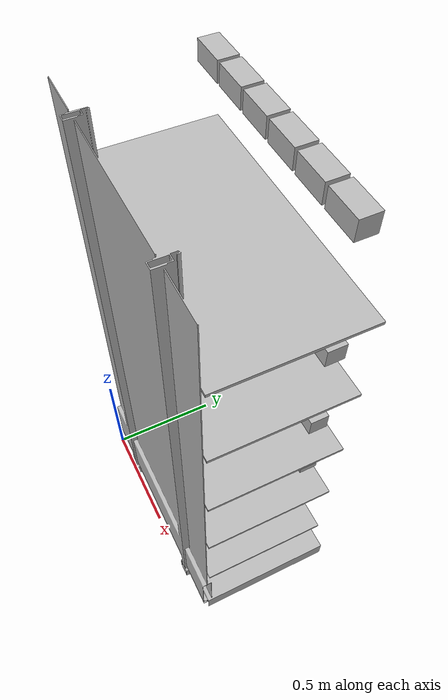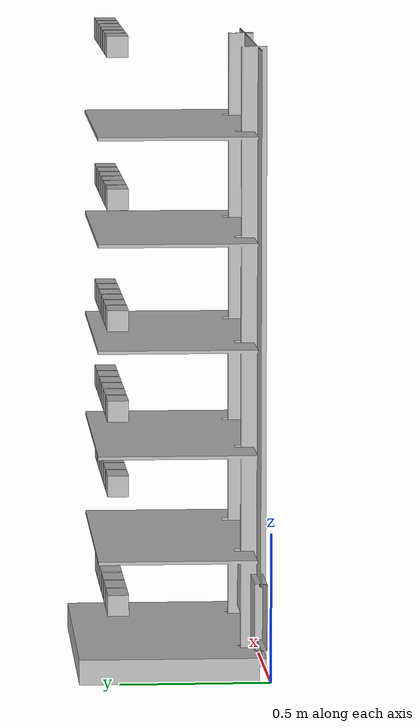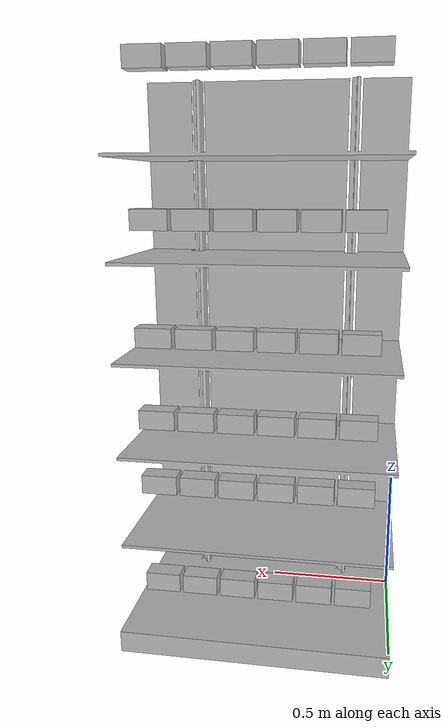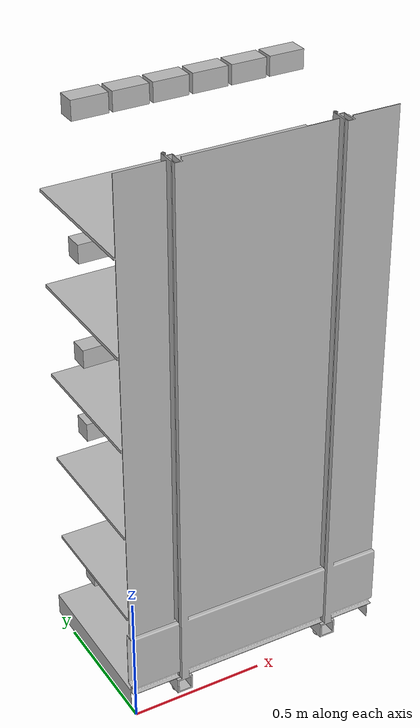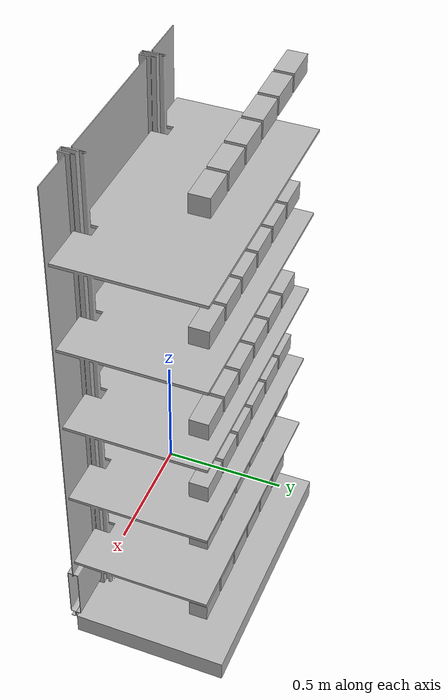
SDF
<?xml version="1.0"?>
<sdf version='1.6'>
  <model name='AH_shelf_filled_thee'>
    <static>1</static>
    <link name='link'>
      <inertial>
        <mass>1</mass>
        <inertia>
          <ixx>1</ixx>
          <ixy>0</ixy>
          <ixz>0</ixz>
          <iyy>1</iyy>
          <iyz>0</iyz>
          <izz>1</izz>
        </inertia>
      </inertial>
      <pose frame=''>-0 0 0 0 0 0</pose>

      <visual name='visual'>
        <pose frame=''>0 0 0 0 0 0</pose>
        <geometry>
          <mesh>
            <uri>model://AH_shelf/AH_shelf.dae</uri>
            <scale>1 1 1</scale>
          </mesh>
        </geometry>
        <transparency>0</transparency>
        <cast_shadows>1</cast_shadows>
      </visual>

      <collision name='collision'>
        <laser_retro>0</laser_retro>
        <max_contacts>10</max_contacts>
        <pose frame=''>0 0 0 0 -0 0</pose>
        <geometry>
          <mesh>
            <uri>model://AH_shelf/AH_shelf.dae</uri>
            <scale>1 1 1</scale>
          </mesh>
        </geometry>
        <surface>
          <friction>
            <ode>
              <mu>1</mu>
              <mu2>1</mu2>
              <fdir1>0 0 0</fdir1>
              <slip1>0</slip1>
              <slip2>0</slip2>
            </ode>
            <torsional>
              <coefficient>1</coefficient>
              <patch_radius>0</patch_radius>
              <surface_radius>0</surface_radius>
              <use_patch_radius>1</use_patch_radius>
              <ode>
                <slip>0</slip>
              </ode>
            </torsional>
          </friction>
          <bounce>
            <restitution_coefficient>0</restitution_coefficient>
            <threshold>1e+06</threshold>
          </bounce>
          <contact>
            <collide_without_contact>0</collide_without_contact>
            <collide_without_contact_bitmask>1</collide_without_contact_bitmask>
            <collide_bitmask>1</collide_bitmask>
            <ode>
              <soft_cfm>0</soft_cfm>
              <soft_erp>0.2</soft_erp>
              <kp>1e+13</kp>
              <kd>1</kd>
              <max_vel>0.01</max_vel>
              <min_depth>0</min_depth>
            </ode>
            <bullet>
              <split_impulse>1</split_impulse>
              <split_impulse_penetration_threshold>-0.01</split_impulse_penetration_threshold>
              <soft_cfm>0</soft_cfm>
              <soft_erp>0.2</soft_erp>
              <kp>1e+13</kp>
              <kd>1</kd>
            </bullet>
          </contact>
        </surface>
      </collision>
    </link>

  <model name="board0">
    <pose>0 0.5 2.1 0 0 0</pose>

    <include>
      <uri>model://AH_thee_bosvruchten_tag36_11_00100</uri>
      <pose>0.14285714285714285 0 0 0 0 1.57</pose>
    </include>

    <include>
      <uri>model://AH_thee_bosvruchten_tag36_11_00101</uri>
      <pose>0.2857142857142857 0 0 0 0 1.57</pose>
    </include>

    <include>
      <uri>model://AH_thee_bosvruchten_tag36_11_00102</uri>
      <pose>0.42857142857142855 0 0 0 0 1.57</pose>
    </include>

    <include>
      <uri>model://AH_thee_bosvruchten_tag36_11_00103</uri>
      <pose>0.5714285714285714 0 0 0 0 1.57</pose>
    </include>

    <include>
      <uri>model://AH_thee_bosvruchten_tag36_11_00104</uri>
      <pose>0.7142857142857142 0 0 0 0 1.57</pose>
    </include>

    <include>
      <uri>model://AH_thee_bosvruchten_tag36_11_00105</uri>
      <pose>0.8571428571428571 0 0 0 0 1.57</pose>
    </include>

  </model>

  <model name="board1">
    <pose>0 0.5 1.6 0 0 0</pose>

    <include>
      <uri>model://AH_thee_bosvruchten_tag36_11_00106</uri>
      <pose>0.14285714285714285 0 0 0 0 1.57</pose>
    </include>

    <include>
      <uri>model://AH_thee_bosvruchten_tag36_11_00107</uri>
      <pose>0.2857142857142857 0 0 0 0 1.57</pose>
    </include>

    <include>
      <uri>model://AH_thee_bosvruchten_tag36_11_00108</uri>
      <pose>0.42857142857142855 0 0 0 0 1.57</pose>
    </include>

    <include>
      <uri>model://AH_thee_bosvruchten_tag36_11_00109</uri>
      <pose>0.5714285714285714 0 0 0 0 1.57</pose>
    </include>

    <include>
      <uri>model://AH_thee_bosvruchten_tag36_11_00111</uri>
      <pose>0.7142857142857142 0 0 0 0 1.57</pose>
    </include>

    <include>
      <uri>model://AH_thee_bosvruchten_tag36_11_00112</uri>
      <pose>0.8571428571428571 0 0 0 0 1.57</pose>
    </include>

  </model>

  <model name="board2">
    <pose>0 0.5 1.2 0 0 0</pose>

    <include>
      <uri>model://AH_thee_bosvruchten_tag36_11_00113</uri>
      <pose>0.14285714285714285 0 0 0 0 1.57</pose>
    </include>

    <include>
      <uri>model://AH_thee_bosvruchten_tag36_11_00114</uri>
      <pose>0.2857142857142857 0 0 0 0 1.57</pose>
    </include>

    <include>
      <uri>model://AH_thee_bosvruchten_tag36_11_00115</uri>
      <pose>0.42857142857142855 0 0 0 0 1.57</pose>
    </include>

    <include>
      <uri>model://AH_thee_bosvruchten_tag36_11_00116</uri>
      <pose>0.5714285714285714 0 0 0 0 1.57</pose>
    </include>

    <include>
      <uri>model://AH_thee_bosvruchten_tag36_11_00117</uri>
      <pose>0.7142857142857142 0 0 0 0 1.57</pose>
    </include>

    <include>
      <uri>model://AH_thee_bosvruchten_tag36_11_00118</uri>
      <pose>0.8571428571428571 0 0 0 0 1.57</pose>
    </include>

  </model>

  <model name="board3">
    <pose>0 0.5 0.9 0 0 0</pose>

    <include>
      <uri>model://AH_thee_mango_tag36_11_00121</uri>
      <pose>0.14285714285714285 0 0 0 0 1.57</pose>
    </include>

    <include>
      <uri>model://AH_thee_mango_tag36_11_00122</uri>
      <pose>0.2857142857142857 0 0 0 0 1.57</pose>
    </include>

    <include>
      <uri>model://AH_thee_mango_tag36_11_00123</uri>
      <pose>0.42857142857142855 0 0 0 0 1.57</pose>
    </include>

    <include>
      <uri>model://AH_thee_mango_tag36_11_00124</uri>
      <pose>0.5714285714285714 0 0 0 0 1.57</pose>
    </include>

    <include>
      <uri>model://AH_thee_mango_tag36_11_00125</uri>
      <pose>0.7142857142857142 0 0 0 0 1.57</pose>
    </include>

    <include>
      <uri>model://AH_thee_mango_tag36_11_00126</uri>
      <pose>0.8571428571428571 0 0 0 0 1.57</pose>
    </include>

  </model>

  <model name="board4">
    <pose>0 0.5 0.65 0 0 0</pose>

    <include>
      <uri>model://AH_thee_mango_tag36_11_00127</uri>
      <pose>0.14285714285714285 0 0 0 0 1.57</pose>
    </include>

    <include>
      <uri>model://AH_thee_mango_tag36_11_00128</uri>
      <pose>0.2857142857142857 0 0 0 0 1.57</pose>
    </include>

    <include>
      <uri>model://AH_thee_mango_tag36_11_00129</uri>
      <pose>0.42857142857142855 0 0 0 0 1.57</pose>
    </include>

    <include>
      <uri>model://AH_thee_mango_tag36_11_00130</uri>
      <pose>0.5714285714285714 0 0 0 0 1.57</pose>
    </include>

    <include>
      <uri>model://AH_thee_mango_tag36_11_00131</uri>
      <pose>0.7142857142857142 0 0 0 0 1.57</pose>
    </include>

    <include>
      <uri>model://AH_thee_mango_tag36_11_00132</uri>
      <pose>0.8571428571428571 0 0 0 0 1.57</pose>
    </include>

  </model>

  <model name="board5">
    <pose>0 0.5 0.25 0 0 0</pose>

    <include>
      <uri>model://AH_thee_mango_tag36_11_00133</uri>
      <pose>0.14285714285714285 0 0 0 0 1.57</pose>
    </include>

    <include>
      <uri>model://AH_thee_mango_tag36_11_00134</uri>
      <pose>0.2857142857142857 0 0 0 0 1.57</pose>
    </include>

    <include>
      <uri>model://AH_thee_mango_tag36_11_00135</uri>
      <pose>0.42857142857142855 0 0 0 0 1.57</pose>
    </include>

    <include>
      <uri>model://AH_thee_mango_tag36_11_00136</uri>
      <pose>0.5714285714285714 0 0 0 0 1.57</pose>
    </include>

    <include>
      <uri>model://AH_thee_mango_tag36_11_00137</uri>
      <pose>0.7142857142857142 0 0 0 0 1.57</pose>
    </include>

    <include>
      <uri>model://AH_thee_mango_tag36_11_00138</uri>
      <pose>0.8571428571428571 0 0 0 0 1.57</pose>
    </include>

  </model>

  </model>
</sdf>

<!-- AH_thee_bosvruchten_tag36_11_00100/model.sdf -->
<sdf version='1.6'>
  <model name='AH_thee_bosvruchten_tag36_11_00100'>
    <static>0</static>
    <link name='link_0'>

      <inertial>
        <mass>0.1</mass>
        <inertia>
          <ixx>1.4e-03</ixx>
          <ixy>0</ixy>
          <ixz>0</ixz>
          <iyy>1.4e-03</iyy>
          <iyz>0</iyz>
          <izz>2.8e-03</izz>
        </inertia>
      </inertial>

      <pose frame=''>-0 0 0 0 -0 0</pose>

      <visual name='visual'>
        <pose frame=''>0 0 0 0 -0 0</pose>
        <geometry>
          <mesh>
            <uri>model://AH_thee_bosvruchten/AH_thee_bosvruchten_tag36_11_00100/AH_thee_bosvruchten_tag36_11_00100.dae</uri>
            <scale>1 1 1</scale>
          </mesh>
        </geometry>
        <transparency>0</transparency>
        <cast_shadows>1</cast_shadows>
      </visual>

      <collision name='collision'>
        <laser_retro>0</laser_retro>
        <max_contacts>10</max_contacts>
        <pose frame=''>0 0 0 0 -0 0</pose>
        <geometry>
          <mesh>
            <uri>model://AH_thee_bosvruchten/AH_thee_bosvruchten_tag36_11_00100/AH_thee_bosvruchten_tag36_11_00100.dae</uri>
            <scale>1 1 1</scale>
          </mesh>
        </geometry>
        <surface>
          <friction>
            <ode>
              <mu>1</mu>
              <mu2>1</mu2>
              <fdir1>0 0 0</fdir1>
              <slip1>0</slip1>
              <slip2>0</slip2>
            </ode>
            <torsional>
              <coefficient>1</coefficient>
              <patch_radius>0</patch_radius>
              <surface_radius>0</surface_radius>
              <use_patch_radius>1</use_patch_radius>
              <ode>
                <slip>0</slip>
              </ode>
            </torsional>
          </friction>
          <bounce>
            <restitution_coefficient>0</restitution_coefficient>
            <threshold>1e+06</threshold>
          </bounce>
          <contact>
            <collide_without_contact>0</collide_without_contact>
            <collide_without_contact_bitmask>1</collide_without_contact_bitmask>
            <collide_bitmask>1</collide_bitmask>
            <ode>
              <soft_cfm>0</soft_cfm>
              <soft_erp>0.2</soft_erp>
              <kp>1e+13</kp>
              <kd>1</kd>
              <max_vel>0.01</max_vel>
              <min_depth>0</min_depth>
            </ode>
            <bullet>
              <split_impulse>1</split_impulse>
              <split_impulse_penetration_threshold>-0.01</split_impulse_penetration_threshold>
              <soft_cfm>0</soft_cfm>
              <soft_erp>0.2</soft_erp>
              <kp>1e+13</kp>
              <kd>1</kd>
            </bullet>
          </contact>
        </surface>
      </collision>

    </link>
  </model>
</sdf>

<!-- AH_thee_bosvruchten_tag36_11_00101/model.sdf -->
<sdf version='1.6'>
  <model name='AH_thee_bosvruchten_tag36_11_00101'>
    <static>0</static>
    <link name='link_0'>

      <inertial>
        <mass>0.1</mass>
        <inertia>
          <ixx>1.4e-03</ixx>
          <ixy>0</ixy>
          <ixz>0</ixz>
          <iyy>1.4e-03</iyy>
          <iyz>0</iyz>
          <izz>2.8e-03</izz>
        </inertia>
      </inertial>

      <pose frame=''>-0 0 0 0 -0 0</pose>

      <visual name='visual'>
        <pose frame=''>0 0 0 0 -0 0</pose>
        <geometry>
          <mesh>
            <uri>model://AH_thee_bosvruchten/AH_thee_bosvruchten_tag36_11_00101/AH_thee_bosvruchten_tag36_11_00101.dae</uri>
            <scale>1 1 1</scale>
          </mesh>
        </geometry>
        <transparency>0</transparency>
        <cast_shadows>1</cast_shadows>
      </visual>

      <collision name='collision'>
        <laser_retro>0</laser_retro>
        <max_contacts>10</max_contacts>
        <pose frame=''>0 0 0 0 -0 0</pose>
        <geometry>
          <mesh>
            <uri>model://AH_thee_bosvruchten/AH_thee_bosvruchten_tag36_11_00101/AH_thee_bosvruchten_tag36_11_00101.dae</uri>
            <scale>1 1 1</scale>
          </mesh>
        </geometry>
        <surface>
          <friction>
            <ode>
              <mu>1</mu>
              <mu2>1</mu2>
              <fdir1>0 0 0</fdir1>
              <slip1>0</slip1>
              <slip2>0</slip2>
            </ode>
            <torsional>
              <coefficient>1</coefficient>
              <patch_radius>0</patch_radius>
              <surface_radius>0</surface_radius>
              <use_patch_radius>1</use_patch_radius>
              <ode>
                <slip>0</slip>
              </ode>
            </torsional>
          </friction>
          <bounce>
            <restitution_coefficient>0</restitution_coefficient>
            <threshold>1e+06</threshold>
          </bounce>
          <contact>
            <collide_without_contact>0</collide_without_contact>
            <collide_without_contact_bitmask>1</collide_without_contact_bitmask>
            <collide_bitmask>1</collide_bitmask>
            <ode>
              <soft_cfm>0</soft_cfm>
              <soft_erp>0.2</soft_erp>
              <kp>1e+13</kp>
              <kd>1</kd>
              <max_vel>0.01</max_vel>
              <min_depth>0</min_depth>
            </ode>
            <bullet>
              <split_impulse>1</split_impulse>
              <split_impulse_penetration_threshold>-0.01</split_impulse_penetration_threshold>
              <soft_cfm>0</soft_cfm>
              <soft_erp>0.2</soft_erp>
              <kp>1e+13</kp>
              <kd>1</kd>
            </bullet>
          </contact>
        </surface>
      </collision>

    </link>
  </model>
</sdf>

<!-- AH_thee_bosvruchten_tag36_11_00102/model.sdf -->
<sdf version='1.6'>
  <model name='AH_thee_bosvruchten_tag36_11_00102'>
    <static>0</static>
    <link name='link_0'>

      <inertial>
        <mass>0.1</mass>
        <inertia>
          <ixx>1.4e-03</ixx>
          <ixy>0</ixy>
          <ixz>0</ixz>
          <iyy>1.4e-03</iyy>
          <iyz>0</iyz>
          <izz>2.8e-03</izz>
        </inertia>
      </inertial>

      <pose frame=''>-0 0 0 0 -0 0</pose>

      <visual name='visual'>
        <pose frame=''>0 0 0 0 -0 0</pose>
        <geometry>
          <mesh>
            <uri>model://AH_thee_bosvruchten/AH_thee_bosvruchten_tag36_11_00102/AH_thee_bosvruchten_tag36_11_00102.dae</uri>
            <scale>1 1 1</scale>
          </mesh>
        </geometry>
        <transparency>0</transparency>
        <cast_shadows>1</cast_shadows>
      </visual>

      <collision name='collision'>
        <laser_retro>0</laser_retro>
        <max_contacts>10</max_contacts>
        <pose frame=''>0 0 0 0 -0 0</pose>
        <geometry>
          <mesh>
            <uri>model://AH_thee_bosvruchten/AH_thee_bosvruchten_tag36_11_00102/AH_thee_bosvruchten_tag36_11_00102.dae</uri>
            <scale>1 1 1</scale>
          </mesh>
        </geometry>
        <surface>
          <friction>
            <ode>
              <mu>1</mu>
              <mu2>1</mu2>
              <fdir1>0 0 0</fdir1>
              <slip1>0</slip1>
              <slip2>0</slip2>
            </ode>
            <torsional>
              <coefficient>1</coefficient>
              <patch_radius>0</patch_radius>
              <surface_radius>0</surface_radius>
              <use_patch_radius>1</use_patch_radius>
              <ode>
                <slip>0</slip>
              </ode>
            </torsional>
          </friction>
          <bounce>
            <restitution_coefficient>0</restitution_coefficient>
            <threshold>1e+06</threshold>
          </bounce>
          <contact>
            <collide_without_contact>0</collide_without_contact>
            <collide_without_contact_bitmask>1</collide_without_contact_bitmask>
            <collide_bitmask>1</collide_bitmask>
            <ode>
              <soft_cfm>0</soft_cfm>
              <soft_erp>0.2</soft_erp>
              <kp>1e+13</kp>
              <kd>1</kd>
              <max_vel>0.01</max_vel>
              <min_depth>0</min_depth>
            </ode>
            <bullet>
              <split_impulse>1</split_impulse>
              <split_impulse_penetration_threshold>-0.01</split_impulse_penetration_threshold>
              <soft_cfm>0</soft_cfm>
              <soft_erp>0.2</soft_erp>
              <kp>1e+13</kp>
              <kd>1</kd>
            </bullet>
          </contact>
        </surface>
      </collision>

    </link>
  </model>
</sdf>

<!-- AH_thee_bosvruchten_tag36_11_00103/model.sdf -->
<sdf version='1.6'>
  <model name='AH_thee_bosvruchten_tag36_11_00103'>
    <static>0</static>
    <link name='link_0'>

      <inertial>
        <mass>0.1</mass>
        <inertia>
          <ixx>1.4e-03</ixx>
          <ixy>0</ixy>
          <ixz>0</ixz>
          <iyy>1.4e-03</iyy>
          <iyz>0</iyz>
          <izz>2.8e-03</izz>
        </inertia>
      </inertial>

      <pose frame=''>-0 0 0 0 -0 0</pose>

      <visual name='visual'>
        <pose frame=''>0 0 0 0 -0 0</pose>
        <geometry>
          <mesh>
            <uri>model://AH_thee_bosvruchten/AH_thee_bosvruchten_tag36_11_00103/AH_thee_bosvruchten_tag36_11_00103.dae</uri>
            <scale>1 1 1</scale>
          </mesh>
        </geometry>
        <transparency>0</transparency>
        <cast_shadows>1</cast_shadows>
      </visual>

      <collision name='collision'>
        <laser_retro>0</laser_retro>
        <max_contacts>10</max_contacts>
        <pose frame=''>0 0 0 0 -0 0</pose>
        <geometry>
          <mesh>
            <uri>model://AH_thee_bosvruchten/AH_thee_bosvruchten_tag36_11_00103/AH_thee_bosvruchten_tag36_11_00103.dae</uri>
            <scale>1 1 1</scale>
          </mesh>
        </geometry>
        <surface>
          <friction>
            <ode>
              <mu>1</mu>
              <mu2>1</mu2>
              <fdir1>0 0 0</fdir1>
              <slip1>0</slip1>
              <slip2>0</slip2>
            </ode>
            <torsional>
              <coefficient>1</coefficient>
              <patch_radius>0</patch_radius>
              <surface_radius>0</surface_radius>
              <use_patch_radius>1</use_patch_radius>
              <ode>
                <slip>0</slip>
              </ode>
            </torsional>
          </friction>
          <bounce>
            <restitution_coefficient>0</restitution_coefficient>
            <threshold>1e+06</threshold>
          </bounce>
          <contact>
            <collide_without_contact>0</collide_without_contact>
            <collide_without_contact_bitmask>1</collide_without_contact_bitmask>
            <collide_bitmask>1</collide_bitmask>
            <ode>
              <soft_cfm>0</soft_cfm>
              <soft_erp>0.2</soft_erp>
              <kp>1e+13</kp>
              <kd>1</kd>
              <max_vel>0.01</max_vel>
              <min_depth>0</min_depth>
            </ode>
            <bullet>
              <split_impulse>1</split_impulse>
              <split_impulse_penetration_threshold>-0.01</split_impulse_penetration_threshold>
              <soft_cfm>0</soft_cfm>
              <soft_erp>0.2</soft_erp>
              <kp>1e+13</kp>
              <kd>1</kd>
            </bullet>
          </contact>
        </surface>
      </collision>

    </link>
  </model>
</sdf>

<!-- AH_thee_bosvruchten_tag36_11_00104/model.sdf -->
<sdf version='1.6'>
  <model name='AH_thee_bosvruchten_tag36_11_00104'>
    <static>0</static>
    <link name='link_0'>

      <inertial>
        <mass>0.1</mass>
        <inertia>
          <ixx>1.4e-03</ixx>
          <ixy>0</ixy>
          <ixz>0</ixz>
          <iyy>1.4e-03</iyy>
          <iyz>0</iyz>
          <izz>2.8e-03</izz>
        </inertia>
      </inertial>

      <pose frame=''>-0 0 0 0 -0 0</pose>

      <visual name='visual'>
        <pose frame=''>0 0 0 0 -0 0</pose>
        <geometry>
          <mesh>
            <uri>model://AH_thee_bosvruchten/AH_thee_bosvruchten_tag36_11_00104/AH_thee_bosvruchten_tag36_11_00104.dae</uri>
            <scale>1 1 1</scale>
          </mesh>
        </geometry>
        <transparency>0</transparency>
        <cast_shadows>1</cast_shadows>
      </visual>

      <collision name='collision'>
        <laser_retro>0</laser_retro>
        <max_contacts>10</max_contacts>
        <pose frame=''>0 0 0 0 -0 0</pose>
        <geometry>
          <mesh>
            <uri>model://AH_thee_bosvruchten/AH_thee_bosvruchten_tag36_11_00104/AH_thee_bosvruchten_tag36_11_00104.dae</uri>
            <scale>1 1 1</scale>
          </mesh>
        </geometry>
        <surface>
          <friction>
            <ode>
              <mu>1</mu>
              <mu2>1</mu2>
              <fdir1>0 0 0</fdir1>
              <slip1>0</slip1>
              <slip2>0</slip2>
            </ode>
            <torsional>
              <coefficient>1</coefficient>
              <patch_radius>0</patch_radius>
              <surface_radius>0</surface_radius>
              <use_patch_radius>1</use_patch_radius>
              <ode>
                <slip>0</slip>
              </ode>
            </torsional>
          </friction>
          <bounce>
            <restitution_coefficient>0</restitution_coefficient>
            <threshold>1e+06</threshold>
          </bounce>
          <contact>
            <collide_without_contact>0</collide_without_contact>
            <collide_without_contact_bitmask>1</collide_without_contact_bitmask>
            <collide_bitmask>1</collide_bitmask>
            <ode>
              <soft_cfm>0</soft_cfm>
              <soft_erp>0.2</soft_erp>
              <kp>1e+13</kp>
              <kd>1</kd>
              <max_vel>0.01</max_vel>
              <min_depth>0</min_depth>
            </ode>
            <bullet>
              <split_impulse>1</split_impulse>
              <split_impulse_penetration_threshold>-0.01</split_impulse_penetration_threshold>
              <soft_cfm>0</soft_cfm>
              <soft_erp>0.2</soft_erp>
              <kp>1e+13</kp>
              <kd>1</kd>
            </bullet>
          </contact>
        </surface>
      </collision>

    </link>
  </model>
</sdf>

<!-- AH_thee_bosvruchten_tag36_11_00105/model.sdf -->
<sdf version='1.6'>
  <model name='AH_thee_bosvruchten_tag36_11_00105'>
    <static>0</static>
    <link name='link_0'>

      <inertial>
        <mass>0.1</mass>
        <inertia>
          <ixx>1.4e-03</ixx>
          <ixy>0</ixy>
          <ixz>0</ixz>
          <iyy>1.4e-03</iyy>
          <iyz>0</iyz>
          <izz>2.8e-03</izz>
        </inertia>
      </inertial>

      <pose frame=''>-0 0 0 0 -0 0</pose>

      <visual name='visual'>
        <pose frame=''>0 0 0 0 -0 0</pose>
        <geometry>
          <mesh>
            <uri>model://AH_thee_bosvruchten/AH_thee_bosvruchten_tag36_11_00105/AH_thee_bosvruchten_tag36_11_00105.dae</uri>
            <scale>1 1 1</scale>
          </mesh>
        </geometry>
        <transparency>0</transparency>
        <cast_shadows>1</cast_shadows>
      </visual>

      <collision name='collision'>
        <laser_retro>0</laser_retro>
        <max_contacts>10</max_contacts>
        <pose frame=''>0 0 0 0 -0 0</pose>
        <geometry>
          <mesh>
            <uri>model://AH_thee_bosvruchten/AH_thee_bosvruchten_tag36_11_00105/AH_thee_bosvruchten_tag36_11_00105.dae</uri>
            <scale>1 1 1</scale>
          </mesh>
        </geometry>
        <surface>
          <friction>
            <ode>
              <mu>1</mu>
              <mu2>1</mu2>
              <fdir1>0 0 0</fdir1>
              <slip1>0</slip1>
              <slip2>0</slip2>
            </ode>
            <torsional>
              <coefficient>1</coefficient>
              <patch_radius>0</patch_radius>
              <surface_radius>0</surface_radius>
              <use_patch_radius>1</use_patch_radius>
              <ode>
                <slip>0</slip>
              </ode>
            </torsional>
          </friction>
          <bounce>
            <restitution_coefficient>0</restitution_coefficient>
            <threshold>1e+06</threshold>
          </bounce>
          <contact>
            <collide_without_contact>0</collide_without_contact>
            <collide_without_contact_bitmask>1</collide_without_contact_bitmask>
            <collide_bitmask>1</collide_bitmask>
            <ode>
              <soft_cfm>0</soft_cfm>
              <soft_erp>0.2</soft_erp>
              <kp>1e+13</kp>
              <kd>1</kd>
              <max_vel>0.01</max_vel>
              <min_depth>0</min_depth>
            </ode>
            <bullet>
              <split_impulse>1</split_impulse>
              <split_impulse_penetration_threshold>-0.01</split_impulse_penetration_threshold>
              <soft_cfm>0</soft_cfm>
              <soft_erp>0.2</soft_erp>
              <kp>1e+13</kp>
              <kd>1</kd>
            </bullet>
          </contact>
        </surface>
      </collision>

    </link>
  </model>
</sdf>

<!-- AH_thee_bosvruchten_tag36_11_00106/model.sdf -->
<sdf version='1.6'>
  <model name='AH_thee_bosvruchten_tag36_11_00106'>
    <static>0</static>
    <link name='link_0'>

      <inertial>
        <mass>0.1</mass>
        <inertia>
          <ixx>1.4e-03</ixx>
          <ixy>0</ixy>
          <ixz>0</ixz>
          <iyy>1.4e-03</iyy>
          <iyz>0</iyz>
          <izz>2.8e-03</izz>
        </inertia>
      </inertial>

      <pose frame=''>-0 0 0 0 -0 0</pose>

      <visual name='visual'>
        <pose frame=''>0 0 0 0 -0 0</pose>
        <geometry>
          <mesh>
            <uri>model://AH_thee_bosvruchten/AH_thee_bosvruchten_tag36_11_00106/AH_thee_bosvruchten_tag36_11_00106.dae</uri>
            <scale>1 1 1</scale>
          </mesh>
        </geometry>
        <transparency>0</transparency>
        <cast_shadows>1</cast_shadows>
      </visual>

      <collision name='collision'>
        <laser_retro>0</laser_retro>
        <max_contacts>10</max_contacts>
        <pose frame=''>0 0 0 0 -0 0</pose>
        <geometry>
          <mesh>
            <uri>model://AH_thee_bosvruchten/AH_thee_bosvruchten_tag36_11_00106/AH_thee_bosvruchten_tag36_11_00106.dae</uri>
            <scale>1 1 1</scale>
          </mesh>
        </geometry>
        <surface>
          <friction>
            <ode>
              <mu>1</mu>
              <mu2>1</mu2>
              <fdir1>0 0 0</fdir1>
              <slip1>0</slip1>
              <slip2>0</slip2>
            </ode>
            <torsional>
              <coefficient>1</coefficient>
              <patch_radius>0</patch_radius>
              <surface_radius>0</surface_radius>
              <use_patch_radius>1</use_patch_radius>
              <ode>
                <slip>0</slip>
              </ode>
            </torsional>
          </friction>
          <bounce>
            <restitution_coefficient>0</restitution_coefficient>
            <threshold>1e+06</threshold>
          </bounce>
          <contact>
            <collide_without_contact>0</collide_without_contact>
            <collide_without_contact_bitmask>1</collide_without_contact_bitmask>
            <collide_bitmask>1</collide_bitmask>
            <ode>
              <soft_cfm>0</soft_cfm>
              <soft_erp>0.2</soft_erp>
              <kp>1e+13</kp>
              <kd>1</kd>
              <max_vel>0.01</max_vel>
              <min_depth>0</min_depth>
            </ode>
            <bullet>
              <split_impulse>1</split_impulse>
              <split_impulse_penetration_threshold>-0.01</split_impulse_penetration_threshold>
              <soft_cfm>0</soft_cfm>
              <soft_erp>0.2</soft_erp>
              <kp>1e+13</kp>
              <kd>1</kd>
            </bullet>
          </contact>
        </surface>
      </collision>

    </link>
  </model>
</sdf>

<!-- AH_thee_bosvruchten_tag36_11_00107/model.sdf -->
<sdf version='1.6'>
  <model name='AH_thee_bosvruchten_tag36_11_00107'>
    <static>0</static>
    <link name='link_0'>

      <inertial>
        <mass>0.1</mass>
        <inertia>
          <ixx>1.4e-03</ixx>
          <ixy>0</ixy>
          <ixz>0</ixz>
          <iyy>1.4e-03</iyy>
          <iyz>0</iyz>
          <izz>2.8e-03</izz>
        </inertia>
      </inertial>

      <pose frame=''>-0 0 0 0 -0 0</pose>

      <visual name='visual'>
        <pose frame=''>0 0 0 0 -0 0</pose>
        <geometry>
          <mesh>
            <uri>model://AH_thee_bosvruchten/AH_thee_bosvruchten_tag36_11_00107/AH_thee_bosvruchten_tag36_11_00107.dae</uri>
            <scale>1 1 1</scale>
          </mesh>
        </geometry>
        <transparency>0</transparency>
        <cast_shadows>1</cast_shadows>
      </visual>

      <collision name='collision'>
        <laser_retro>0</laser_retro>
        <max_contacts>10</max_contacts>
        <pose frame=''>0 0 0 0 -0 0</pose>
        <geometry>
          <mesh>
            <uri>model://AH_thee_bosvruchten/AH_thee_bosvruchten_tag36_11_00107/AH_thee_bosvruchten_tag36_11_00107.dae</uri>
            <scale>1 1 1</scale>
          </mesh>
        </geometry>
        <surface>
          <friction>
            <ode>
              <mu>1</mu>
              <mu2>1</mu2>
              <fdir1>0 0 0</fdir1>
              <slip1>0</slip1>
              <slip2>0</slip2>
            </ode>
            <torsional>
              <coefficient>1</coefficient>
              <patch_radius>0</patch_radius>
              <surface_radius>0</surface_radius>
              <use_patch_radius>1</use_patch_radius>
              <ode>
                <slip>0</slip>
              </ode>
            </torsional>
          </friction>
          <bounce>
            <restitution_coefficient>0</restitution_coefficient>
            <threshold>1e+06</threshold>
          </bounce>
          <contact>
            <collide_without_contact>0</collide_without_contact>
            <collide_without_contact_bitmask>1</collide_without_contact_bitmask>
            <collide_bitmask>1</collide_bitmask>
            <ode>
              <soft_cfm>0</soft_cfm>
              <soft_erp>0.2</soft_erp>
              <kp>1e+13</kp>
              <kd>1</kd>
              <max_vel>0.01</max_vel>
              <min_depth>0</min_depth>
            </ode>
            <bullet>
              <split_impulse>1</split_impulse>
              <split_impulse_penetration_threshold>-0.01</split_impulse_penetration_threshold>
              <soft_cfm>0</soft_cfm>
              <soft_erp>0.2</soft_erp>
              <kp>1e+13</kp>
              <kd>1</kd>
            </bullet>
          </contact>
        </surface>
      </collision>

    </link>
  </model>
</sdf>

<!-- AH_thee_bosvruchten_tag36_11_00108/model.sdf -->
<sdf version='1.6'>
  <model name='AH_thee_bosvruchten_tag36_11_00108'>
    <static>0</static>
    <link name='link_0'>

      <inertial>
        <mass>0.1</mass>
        <inertia>
          <ixx>1.4e-03</ixx>
          <ixy>0</ixy>
          <ixz>0</ixz>
          <iyy>1.4e-03</iyy>
          <iyz>0</iyz>
          <izz>2.8e-03</izz>
        </inertia>
      </inertial>

      <pose frame=''>-0 0 0 0 -0 0</pose>

      <visual name='visual'>
        <pose frame=''>0 0 0 0 -0 0</pose>
        <geometry>
          <mesh>
            <uri>model://AH_thee_bosvruchten/AH_thee_bosvruchten_tag36_11_00108/AH_thee_bosvruchten_tag36_11_00108.dae</uri>
            <scale>1 1 1</scale>
          </mesh>
        </geometry>
        <transparency>0</transparency>
        <cast_shadows>1</cast_shadows>
      </visual>

      <collision name='collision'>
        <laser_retro>0</laser_retro>
        <max_contacts>10</max_contacts>
        <pose frame=''>0 0 0 0 -0 0</pose>
        <geometry>
          <mesh>
            <uri>model://AH_thee_bosvruchten/AH_thee_bosvruchten_tag36_11_00108/AH_thee_bosvruchten_tag36_11_00108.dae</uri>
            <scale>1 1 1</scale>
          </mesh>
        </geometry>
        <surface>
          <friction>
            <ode>
              <mu>1</mu>
              <mu2>1</mu2>
              <fdir1>0 0 0</fdir1>
              <slip1>0</slip1>
              <slip2>0</slip2>
            </ode>
            <torsional>
              <coefficient>1</coefficient>
              <patch_radius>0</patch_radius>
              <surface_radius>0</surface_radius>
              <use_patch_radius>1</use_patch_radius>
              <ode>
                <slip>0</slip>
              </ode>
            </torsional>
          </friction>
          <bounce>
            <restitution_coefficient>0</restitution_coefficient>
            <threshold>1e+06</threshold>
          </bounce>
          <contact>
            <collide_without_contact>0</collide_without_contact>
            <collide_without_contact_bitmask>1</collide_without_contact_bitmask>
            <collide_bitmask>1</collide_bitmask>
            <ode>
              <soft_cfm>0</soft_cfm>
              <soft_erp>0.2</soft_erp>
              <kp>1e+13</kp>
              <kd>1</kd>
              <max_vel>0.01</max_vel>
              <min_depth>0</min_depth>
            </ode>
            <bullet>
              <split_impulse>1</split_impulse>
              <split_impulse_penetration_threshold>-0.01</split_impulse_penetration_threshold>
              <soft_cfm>0</soft_cfm>
              <soft_erp>0.2</soft_erp>
              <kp>1e+13</kp>
              <kd>1</kd>
            </bullet>
          </contact>
        </surface>
      </collision>

    </link>
  </model>
</sdf>

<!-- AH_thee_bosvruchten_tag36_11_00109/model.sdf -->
<sdf version='1.6'>
  <model name='AH_thee_bosvruchten_tag36_11_00109'>
    <static>0</static>
    <link name='link_0'>

      <inertial>
        <mass>0.1</mass>
        <inertia>
          <ixx>1.4e-03</ixx>
          <ixy>0</ixy>
          <ixz>0</ixz>
          <iyy>1.4e-03</iyy>
          <iyz>0</iyz>
          <izz>2.8e-03</izz>
        </inertia>
      </inertial>

      <pose frame=''>-0 0 0 0 -0 0</pose>

      <visual name='visual'>
        <pose frame=''>0 0 0 0 -0 0</pose>
        <geometry>
          <mesh>
            <uri>model://AH_thee_bosvruchten/AH_thee_bosvruchten_tag36_11_00109/AH_thee_bosvruchten_tag36_11_00109.dae</uri>
            <scale>1 1 1</scale>
          </mesh>
        </geometry>
        <transparency>0</transparency>
        <cast_shadows>1</cast_shadows>
      </visual>

      <collision name='collision'>
        <laser_retro>0</laser_retro>
        <max_contacts>10</max_contacts>
        <pose frame=''>0 0 0 0 -0 0</pose>
        <geometry>
          <mesh>
            <uri>model://AH_thee_bosvruchten/AH_thee_bosvruchten_tag36_11_00109/AH_thee_bosvruchten_tag36_11_00109.dae</uri>
            <scale>1 1 1</scale>
          </mesh>
        </geometry>
        <surface>
          <friction>
            <ode>
              <mu>1</mu>
              <mu2>1</mu2>
              <fdir1>0 0 0</fdir1>
              <slip1>0</slip1>
              <slip2>0</slip2>
            </ode>
            <torsional>
              <coefficient>1</coefficient>
              <patch_radius>0</patch_radius>
              <surface_radius>0</surface_radius>
              <use_patch_radius>1</use_patch_radius>
              <ode>
                <slip>0</slip>
              </ode>
            </torsional>
          </friction>
          <bounce>
            <restitution_coefficient>0</restitution_coefficient>
            <threshold>1e+06</threshold>
          </bounce>
          <contact>
            <collide_without_contact>0</collide_without_contact>
            <collide_without_contact_bitmask>1</collide_without_contact_bitmask>
            <collide_bitmask>1</collide_bitmask>
            <ode>
              <soft_cfm>0</soft_cfm>
              <soft_erp>0.2</soft_erp>
              <kp>1e+13</kp>
              <kd>1</kd>
              <max_vel>0.01</max_vel>
              <min_depth>0</min_depth>
            </ode>
            <bullet>
              <split_impulse>1</split_impulse>
              <split_impulse_penetration_threshold>-0.01</split_impulse_penetration_threshold>
              <soft_cfm>0</soft_cfm>
              <soft_erp>0.2</soft_erp>
              <kp>1e+13</kp>
              <kd>1</kd>
            </bullet>
          </contact>
        </surface>
      </collision>

    </link>
  </model>
</sdf>

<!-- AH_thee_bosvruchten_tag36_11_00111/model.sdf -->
<sdf version='1.6'>
  <model name='AH_thee_bosvruchten_tag36_11_00111'>
    <static>0</static>
    <link name='link_0'>

      <inertial>
        <mass>0.1</mass>
        <inertia>
          <ixx>1.4e-03</ixx>
          <ixy>0</ixy>
          <ixz>0</ixz>
          <iyy>1.4e-03</iyy>
          <iyz>0</iyz>
          <izz>2.8e-03</izz>
        </inertia>
      </inertial>

      <pose frame=''>-0 0 0 0 -0 0</pose>

      <visual name='visual'>
        <pose frame=''>0 0 0 0 -0 0</pose>
        <geometry>
          <mesh>
            <uri>model://AH_thee_bosvruchten/AH_thee_bosvruchten_tag36_11_00111/AH_thee_bosvruchten_tag36_11_00111.dae</uri>
            <scale>1 1 1</scale>
          </mesh>
        </geometry>
        <transparency>0</transparency>
        <cast_shadows>1</cast_shadows>
      </visual>

      <collision name='collision'>
        <laser_retro>0</laser_retro>
        <max_contacts>10</max_contacts>
        <pose frame=''>0 0 0 0 -0 0</pose>
        <geometry>
          <mesh>
            <uri>model://AH_thee_bosvruchten/AH_thee_bosvruchten_tag36_11_00111/AH_thee_bosvruchten_tag36_11_00111.dae</uri>
            <scale>1 1 1</scale>
          </mesh>
        </geometry>
        <surface>
          <friction>
            <ode>
              <mu>1</mu>
              <mu2>1</mu2>
              <fdir1>0 0 0</fdir1>
              <slip1>0</slip1>
              <slip2>0</slip2>
            </ode>
            <torsional>
              <coefficient>1</coefficient>
              <patch_radius>0</patch_radius>
              <surface_radius>0</surface_radius>
              <use_patch_radius>1</use_patch_radius>
              <ode>
                <slip>0</slip>
              </ode>
            </torsional>
          </friction>
          <bounce>
            <restitution_coefficient>0</restitution_coefficient>
            <threshold>1e+06</threshold>
          </bounce>
          <contact>
            <collide_without_contact>0</collide_without_contact>
            <collide_without_contact_bitmask>1</collide_without_contact_bitmask>
            <collide_bitmask>1</collide_bitmask>
            <ode>
              <soft_cfm>0</soft_cfm>
              <soft_erp>0.2</soft_erp>
              <kp>1e+13</kp>
              <kd>1</kd>
              <max_vel>0.01</max_vel>
              <min_depth>0</min_depth>
            </ode>
            <bullet>
              <split_impulse>1</split_impulse>
              <split_impulse_penetration_threshold>-0.01</split_impulse_penetration_threshold>
              <soft_cfm>0</soft_cfm>
              <soft_erp>0.2</soft_erp>
              <kp>1e+13</kp>
              <kd>1</kd>
            </bullet>
          </contact>
        </surface>
      </collision>

    </link>
  </model>
</sdf>

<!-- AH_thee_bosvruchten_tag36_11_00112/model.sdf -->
<sdf version='1.6'>
  <model name='AH_thee_bosvruchten_tag36_11_00112'>
    <static>0</static>
    <link name='link_0'>

      <inertial>
        <mass>0.1</mass>
        <inertia>
          <ixx>1.4e-03</ixx>
          <ixy>0</ixy>
          <ixz>0</ixz>
          <iyy>1.4e-03</iyy>
          <iyz>0</iyz>
          <izz>2.8e-03</izz>
        </inertia>
      </inertial>

      <pose frame=''>-0 0 0 0 -0 0</pose>

      <visual name='visual'>
        <pose frame=''>0 0 0 0 -0 0</pose>
        <geometry>
          <mesh>
            <uri>model://AH_thee_bosvruchten/AH_thee_bosvruchten_tag36_11_00112/AH_thee_bosvruchten_tag36_11_00112.dae</uri>
            <scale>1 1 1</scale>
          </mesh>
        </geometry>
        <transparency>0</transparency>
        <cast_shadows>1</cast_shadows>
      </visual>

      <collision name='collision'>
        <laser_retro>0</laser_retro>
        <max_contacts>10</max_contacts>
        <pose frame=''>0 0 0 0 -0 0</pose>
        <geometry>
          <mesh>
            <uri>model://AH_thee_bosvruchten/AH_thee_bosvruchten_tag36_11_00112/AH_thee_bosvruchten_tag36_11_00112.dae</uri>
            <scale>1 1 1</scale>
          </mesh>
        </geometry>
        <surface>
          <friction>
            <ode>
              <mu>1</mu>
              <mu2>1</mu2>
              <fdir1>0 0 0</fdir1>
              <slip1>0</slip1>
              <slip2>0</slip2>
            </ode>
            <torsional>
              <coefficient>1</coefficient>
              <patch_radius>0</patch_radius>
              <surface_radius>0</surface_radius>
              <use_patch_radius>1</use_patch_radius>
              <ode>
                <slip>0</slip>
              </ode>
            </torsional>
          </friction>
          <bounce>
            <restitution_coefficient>0</restitution_coefficient>
            <threshold>1e+06</threshold>
          </bounce>
          <contact>
            <collide_without_contact>0</collide_without_contact>
            <collide_without_contact_bitmask>1</collide_without_contact_bitmask>
            <collide_bitmask>1</collide_bitmask>
            <ode>
              <soft_cfm>0</soft_cfm>
              <soft_erp>0.2</soft_erp>
              <kp>1e+13</kp>
              <kd>1</kd>
              <max_vel>0.01</max_vel>
              <min_depth>0</min_depth>
            </ode>
            <bullet>
              <split_impulse>1</split_impulse>
              <split_impulse_penetration_threshold>-0.01</split_impulse_penetration_threshold>
              <soft_cfm>0</soft_cfm>
              <soft_erp>0.2</soft_erp>
              <kp>1e+13</kp>
              <kd>1</kd>
            </bullet>
          </contact>
        </surface>
      </collision>

    </link>
  </model>
</sdf>

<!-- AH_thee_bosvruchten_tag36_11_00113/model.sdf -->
<sdf version='1.6'>
  <model name='AH_thee_bosvruchten_tag36_11_00113'>
    <static>0</static>
    <link name='link_0'>

      <inertial>
        <mass>0.1</mass>
        <inertia>
          <ixx>1.4e-03</ixx>
          <ixy>0</ixy>
          <ixz>0</ixz>
          <iyy>1.4e-03</iyy>
          <iyz>0</iyz>
          <izz>2.8e-03</izz>
        </inertia>
      </inertial>

      <pose frame=''>-0 0 0 0 -0 0</pose>

      <visual name='visual'>
        <pose frame=''>0 0 0 0 -0 0</pose>
        <geometry>
          <mesh>
            <uri>model://AH_thee_bosvruchten/AH_thee_bosvruchten_tag36_11_00113/AH_thee_bosvruchten_tag36_11_00113.dae</uri>
            <scale>1 1 1</scale>
          </mesh>
        </geometry>
        <transparency>0</transparency>
        <cast_shadows>1</cast_shadows>
      </visual>

      <collision name='collision'>
        <laser_retro>0</laser_retro>
        <max_contacts>10</max_contacts>
        <pose frame=''>0 0 0 0 -0 0</pose>
        <geometry>
          <mesh>
            <uri>model://AH_thee_bosvruchten/AH_thee_bosvruchten_tag36_11_00113/AH_thee_bosvruchten_tag36_11_00113.dae</uri>
            <scale>1 1 1</scale>
          </mesh>
        </geometry>
        <surface>
          <friction>
            <ode>
              <mu>1</mu>
              <mu2>1</mu2>
              <fdir1>0 0 0</fdir1>
              <slip1>0</slip1>
              <slip2>0</slip2>
            </ode>
            <torsional>
              <coefficient>1</coefficient>
              <patch_radius>0</patch_radius>
              <surface_radius>0</surface_radius>
              <use_patch_radius>1</use_patch_radius>
              <ode>
                <slip>0</slip>
              </ode>
            </torsional>
          </friction>
          <bounce>
            <restitution_coefficient>0</restitution_coefficient>
            <threshold>1e+06</threshold>
          </bounce>
          <contact>
            <collide_without_contact>0</collide_without_contact>
            <collide_without_contact_bitmask>1</collide_without_contact_bitmask>
            <collide_bitmask>1</collide_bitmask>
            <ode>
              <soft_cfm>0</soft_cfm>
              <soft_erp>0.2</soft_erp>
              <kp>1e+13</kp>
              <kd>1</kd>
              <max_vel>0.01</max_vel>
              <min_depth>0</min_depth>
            </ode>
            <bullet>
              <split_impulse>1</split_impulse>
              <split_impulse_penetration_threshold>-0.01</split_impulse_penetration_threshold>
              <soft_cfm>0</soft_cfm>
              <soft_erp>0.2</soft_erp>
              <kp>1e+13</kp>
              <kd>1</kd>
            </bullet>
          </contact>
        </surface>
      </collision>

    </link>
  </model>
</sdf>

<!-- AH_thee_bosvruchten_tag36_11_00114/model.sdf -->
<sdf version='1.6'>
  <model name='AH_thee_bosvruchten_tag36_11_00114'>
    <static>0</static>
    <link name='link_0'>

      <inertial>
        <mass>0.1</mass>
        <inertia>
          <ixx>1.4e-03</ixx>
          <ixy>0</ixy>
          <ixz>0</ixz>
          <iyy>1.4e-03</iyy>
          <iyz>0</iyz>
          <izz>2.8e-03</izz>
        </inertia>
      </inertial>

      <pose frame=''>-0 0 0 0 -0 0</pose>

      <visual name='visual'>
        <pose frame=''>0 0 0 0 -0 0</pose>
        <geometry>
          <mesh>
            <uri>model://AH_thee_bosvruchten/AH_thee_bosvruchten_tag36_11_00114/AH_thee_bosvruchten_tag36_11_00114.dae</uri>
            <scale>1 1 1</scale>
          </mesh>
        </geometry>
        <transparency>0</transparency>
        <cast_shadows>1</cast_shadows>
      </visual>

      <collision name='collision'>
        <laser_retro>0</laser_retro>
        <max_contacts>10</max_contacts>
        <pose frame=''>0 0 0 0 -0 0</pose>
        <geometry>
          <mesh>
            <uri>model://AH_thee_bosvruchten/AH_thee_bosvruchten_tag36_11_00114/AH_thee_bosvruchten_tag36_11_00114.dae</uri>
            <scale>1 1 1</scale>
          </mesh>
        </geometry>
        <surface>
          <friction>
            <ode>
              <mu>1</mu>
              <mu2>1</mu2>
              <fdir1>0 0 0</fdir1>
              <slip1>0</slip1>
              <slip2>0</slip2>
            </ode>
            <torsional>
              <coefficient>1</coefficient>
              <patch_radius>0</patch_radius>
              <surface_radius>0</surface_radius>
              <use_patch_radius>1</use_patch_radius>
              <ode>
                <slip>0</slip>
              </ode>
            </torsional>
          </friction>
          <bounce>
            <restitution_coefficient>0</restitution_coefficient>
            <threshold>1e+06</threshold>
          </bounce>
          <contact>
            <collide_without_contact>0</collide_without_contact>
            <collide_without_contact_bitmask>1</collide_without_contact_bitmask>
            <collide_bitmask>1</collide_bitmask>
            <ode>
              <soft_cfm>0</soft_cfm>
              <soft_erp>0.2</soft_erp>
              <kp>1e+13</kp>
              <kd>1</kd>
              <max_vel>0.01</max_vel>
              <min_depth>0</min_depth>
            </ode>
            <bullet>
              <split_impulse>1</split_impulse>
              <split_impulse_penetration_threshold>-0.01</split_impulse_penetration_threshold>
              <soft_cfm>0</soft_cfm>
              <soft_erp>0.2</soft_erp>
              <kp>1e+13</kp>
              <kd>1</kd>
            </bullet>
          </contact>
        </surface>
      </collision>

    </link>
  </model>
</sdf>

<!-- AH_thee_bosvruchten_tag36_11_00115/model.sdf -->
<sdf version='1.6'>
  <model name='AH_thee_bosvruchten_tag36_11_00115'>
    <static>0</static>
    <link name='link_0'>

      <inertial>
        <mass>0.1</mass>
        <inertia>
          <ixx>1.4e-03</ixx>
          <ixy>0</ixy>
          <ixz>0</ixz>
          <iyy>1.4e-03</iyy>
          <iyz>0</iyz>
          <izz>2.8e-03</izz>
        </inertia>
      </inertial>

      <pose frame=''>-0 0 0 0 -0 0</pose>

      <visual name='visual'>
        <pose frame=''>0 0 0 0 -0 0</pose>
        <geometry>
          <mesh>
            <uri>model://AH_thee_bosvruchten/AH_thee_bosvruchten_tag36_11_00115/AH_thee_bosvruchten_tag36_11_00115.dae</uri>
            <scale>1 1 1</scale>
          </mesh>
        </geometry>
        <transparency>0</transparency>
        <cast_shadows>1</cast_shadows>
      </visual>

      <collision name='collision'>
        <laser_retro>0</laser_retro>
        <max_contacts>10</max_contacts>
        <pose frame=''>0 0 0 0 -0 0</pose>
        <geometry>
          <mesh>
            <uri>model://AH_thee_bosvruchten/AH_thee_bosvruchten_tag36_11_00115/AH_thee_bosvruchten_tag36_11_00115.dae</uri>
            <scale>1 1 1</scale>
          </mesh>
        </geometry>
        <surface>
          <friction>
            <ode>
              <mu>1</mu>
              <mu2>1</mu2>
              <fdir1>0 0 0</fdir1>
              <slip1>0</slip1>
              <slip2>0</slip2>
            </ode>
            <torsional>
              <coefficient>1</coefficient>
              <patch_radius>0</patch_radius>
              <surface_radius>0</surface_radius>
              <use_patch_radius>1</use_patch_radius>
              <ode>
                <slip>0</slip>
              </ode>
            </torsional>
          </friction>
          <bounce>
            <restitution_coefficient>0</restitution_coefficient>
            <threshold>1e+06</threshold>
          </bounce>
          <contact>
            <collide_without_contact>0</collide_without_contact>
            <collide_without_contact_bitmask>1</collide_without_contact_bitmask>
            <collide_bitmask>1</collide_bitmask>
            <ode>
              <soft_cfm>0</soft_cfm>
              <soft_erp>0.2</soft_erp>
              <kp>1e+13</kp>
              <kd>1</kd>
              <max_vel>0.01</max_vel>
              <min_depth>0</min_depth>
            </ode>
            <bullet>
              <split_impulse>1</split_impulse>
              <split_impulse_penetration_threshold>-0.01</split_impulse_penetration_threshold>
              <soft_cfm>0</soft_cfm>
              <soft_erp>0.2</soft_erp>
              <kp>1e+13</kp>
              <kd>1</kd>
            </bullet>
          </contact>
        </surface>
      </collision>

    </link>
  </model>
</sdf>

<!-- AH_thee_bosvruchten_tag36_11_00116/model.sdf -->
<sdf version='1.6'>
  <model name='AH_thee_bosvruchten_tag36_11_00116'>
    <static>0</static>
    <link name='link_0'>

      <inertial>
        <mass>0.1</mass>
        <inertia>
          <ixx>1.4e-03</ixx>
          <ixy>0</ixy>
          <ixz>0</ixz>
          <iyy>1.4e-03</iyy>
          <iyz>0</iyz>
          <izz>2.8e-03</izz>
        </inertia>
      </inertial>

      <pose frame=''>-0 0 0 0 -0 0</pose>

      <visual name='visual'>
        <pose frame=''>0 0 0 0 -0 0</pose>
        <geometry>
          <mesh>
            <uri>model://AH_thee_bosvruchten/AH_thee_bosvruchten_tag36_11_00116/AH_thee_bosvruchten_tag36_11_00116.dae</uri>
            <scale>1 1 1</scale>
          </mesh>
        </geometry>
        <transparency>0</transparency>
        <cast_shadows>1</cast_shadows>
      </visual>

      <collision name='collision'>
        <laser_retro>0</laser_retro>
        <max_contacts>10</max_contacts>
        <pose frame=''>0 0 0 0 -0 0</pose>
        <geometry>
          <mesh>
            <uri>model://AH_thee_bosvruchten/AH_thee_bosvruchten_tag36_11_00116/AH_thee_bosvruchten_tag36_11_00116.dae</uri>
            <scale>1 1 1</scale>
          </mesh>
        </geometry>
        <surface>
          <friction>
            <ode>
              <mu>1</mu>
              <mu2>1</mu2>
              <fdir1>0 0 0</fdir1>
              <slip1>0</slip1>
              <slip2>0</slip2>
            </ode>
            <torsional>
              <coefficient>1</coefficient>
              <patch_radius>0</patch_radius>
              <surface_radius>0</surface_radius>
              <use_patch_radius>1</use_patch_radius>
              <ode>
                <slip>0</slip>
              </ode>
            </torsional>
          </friction>
          <bounce>
            <restitution_coefficient>0</restitution_coefficient>
            <threshold>1e+06</threshold>
          </bounce>
          <contact>
            <collide_without_contact>0</collide_without_contact>
            <collide_without_contact_bitmask>1</collide_without_contact_bitmask>
            <collide_bitmask>1</collide_bitmask>
            <ode>
              <soft_cfm>0</soft_cfm>
              <soft_erp>0.2</soft_erp>
              <kp>1e+13</kp>
              <kd>1</kd>
              <max_vel>0.01</max_vel>
              <min_depth>0</min_depth>
            </ode>
            <bullet>
              <split_impulse>1</split_impulse>
              <split_impulse_penetration_threshold>-0.01</split_impulse_penetration_threshold>
              <soft_cfm>0</soft_cfm>
              <soft_erp>0.2</soft_erp>
              <kp>1e+13</kp>
              <kd>1</kd>
            </bullet>
          </contact>
        </surface>
      </collision>

    </link>
  </model>
</sdf>

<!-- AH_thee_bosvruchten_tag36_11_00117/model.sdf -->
<sdf version='1.6'>
  <model name='AH_thee_bosvruchten_tag36_11_00117'>
    <static>0</static>
    <link name='link_0'>

      <inertial>
        <mass>0.1</mass>
        <inertia>
          <ixx>1.4e-03</ixx>
          <ixy>0</ixy>
          <ixz>0</ixz>
          <iyy>1.4e-03</iyy>
          <iyz>0</iyz>
          <izz>2.8e-03</izz>
        </inertia>
      </inertial>

      <pose frame=''>-0 0 0 0 -0 0</pose>

      <visual name='visual'>
        <pose frame=''>0 0 0 0 -0 0</pose>
        <geometry>
          <mesh>
            <uri>model://AH_thee_bosvruchten/AH_thee_bosvruchten_tag36_11_00117/AH_thee_bosvruchten_tag36_11_00117.dae</uri>
            <scale>1 1 1</scale>
          </mesh>
        </geometry>
        <transparency>0</transparency>
        <cast_shadows>1</cast_shadows>
      </visual>

      <collision name='collision'>
        <laser_retro>0</laser_retro>
        <max_contacts>10</max_contacts>
        <pose frame=''>0 0 0 0 -0 0</pose>
        <geometry>
          <mesh>
            <uri>model://AH_thee_bosvruchten/AH_thee_bosvruchten_tag36_11_00117/AH_thee_bosvruchten_tag36_11_00117.dae</uri>
            <scale>1 1 1</scale>
          </mesh>
        </geometry>
        <surface>
          <friction>
            <ode>
              <mu>1</mu>
              <mu2>1</mu2>
              <fdir1>0 0 0</fdir1>
              <slip1>0</slip1>
              <slip2>0</slip2>
            </ode>
            <torsional>
              <coefficient>1</coefficient>
              <patch_radius>0</patch_radius>
              <surface_radius>0</surface_radius>
              <use_patch_radius>1</use_patch_radius>
              <ode>
                <slip>0</slip>
              </ode>
            </torsional>
          </friction>
          <bounce>
            <restitution_coefficient>0</restitution_coefficient>
            <threshold>1e+06</threshold>
          </bounce>
          <contact>
            <collide_without_contact>0</collide_without_contact>
            <collide_without_contact_bitmask>1</collide_without_contact_bitmask>
            <collide_bitmask>1</collide_bitmask>
            <ode>
              <soft_cfm>0</soft_cfm>
              <soft_erp>0.2</soft_erp>
              <kp>1e+13</kp>
              <kd>1</kd>
              <max_vel>0.01</max_vel>
              <min_depth>0</min_depth>
            </ode>
            <bullet>
              <split_impulse>1</split_impulse>
              <split_impulse_penetration_threshold>-0.01</split_impulse_penetration_threshold>
              <soft_cfm>0</soft_cfm>
              <soft_erp>0.2</soft_erp>
              <kp>1e+13</kp>
              <kd>1</kd>
            </bullet>
          </contact>
        </surface>
      </collision>

    </link>
  </model>
</sdf>

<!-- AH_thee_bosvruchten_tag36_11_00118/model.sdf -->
<sdf version='1.6'>
  <model name='AH_thee_bosvruchten_tag36_11_00118'>
    <static>0</static>
    <link name='link_0'>

      <inertial>
        <mass>0.1</mass>
        <inertia>
          <ixx>1.4e-03</ixx>
          <ixy>0</ixy>
          <ixz>0</ixz>
          <iyy>1.4e-03</iyy>
          <iyz>0</iyz>
          <izz>2.8e-03</izz>
        </inertia>
      </inertial>

      <pose frame=''>-0 0 0 0 -0 0</pose>

      <visual name='visual'>
        <pose frame=''>0 0 0 0 -0 0</pose>
        <geometry>
          <mesh>
            <uri>model://AH_thee_bosvruchten/AH_thee_bosvruchten_tag36_11_00118/AH_thee_bosvruchten_tag36_11_00118.dae</uri>
            <scale>1 1 1</scale>
          </mesh>
        </geometry>
        <transparency>0</transparency>
        <cast_shadows>1</cast_shadows>
      </visual>

      <collision name='collision'>
        <laser_retro>0</laser_retro>
        <max_contacts>10</max_contacts>
        <pose frame=''>0 0 0 0 -0 0</pose>
        <geometry>
          <mesh>
            <uri>model://AH_thee_bosvruchten/AH_thee_bosvruchten_tag36_11_00118/AH_thee_bosvruchten_tag36_11_00118.dae</uri>
            <scale>1 1 1</scale>
          </mesh>
        </geometry>
        <surface>
          <friction>
            <ode>
              <mu>1</mu>
              <mu2>1</mu2>
              <fdir1>0 0 0</fdir1>
              <slip1>0</slip1>
              <slip2>0</slip2>
            </ode>
            <torsional>
              <coefficient>1</coefficient>
              <patch_radius>0</patch_radius>
              <surface_radius>0</surface_radius>
              <use_patch_radius>1</use_patch_radius>
              <ode>
                <slip>0</slip>
              </ode>
            </torsional>
          </friction>
          <bounce>
            <restitution_coefficient>0</restitution_coefficient>
            <threshold>1e+06</threshold>
          </bounce>
          <contact>
            <collide_without_contact>0</collide_without_contact>
            <collide_without_contact_bitmask>1</collide_without_contact_bitmask>
            <collide_bitmask>1</collide_bitmask>
            <ode>
              <soft_cfm>0</soft_cfm>
              <soft_erp>0.2</soft_erp>
              <kp>1e+13</kp>
              <kd>1</kd>
              <max_vel>0.01</max_vel>
              <min_depth>0</min_depth>
            </ode>
            <bullet>
              <split_impulse>1</split_impulse>
              <split_impulse_penetration_threshold>-0.01</split_impulse_penetration_threshold>
              <soft_cfm>0</soft_cfm>
              <soft_erp>0.2</soft_erp>
              <kp>1e+13</kp>
              <kd>1</kd>
            </bullet>
          </contact>
        </surface>
      </collision>

    </link>
  </model>
</sdf>

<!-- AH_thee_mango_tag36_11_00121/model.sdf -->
<sdf version='1.6'>
  <model name='AH_thee_mango_tag36_11_00121'>
    <static>0</static>
    <link name='link_0'>

      <inertial>
        <mass>0.1</mass>
        <inertia>
          <ixx>1.4e-03</ixx>
          <ixy>0</ixy>
          <ixz>0</ixz>
          <iyy>1.4e-03</iyy>
          <iyz>0</iyz>
          <izz>2.8e-03</izz>
        </inertia>
      </inertial>

      <pose frame=''>-0 0 0 0 -0 0</pose>

      <visual name='visual'>
        <pose frame=''>0 0 0 0 -0 0</pose>
        <geometry>
          <mesh>
            <uri>model://AH_thee_mango/AH_thee_mango_tag36_11_00121/AH_thee_mango_tag36_11_00121.dae</uri>
            <scale>1 1 1</scale>
          </mesh>
        </geometry>
        <transparency>0</transparency>
        <cast_shadows>1</cast_shadows>
      </visual>

      <collision name='collision'>
        <laser_retro>0</laser_retro>
        <max_contacts>10</max_contacts>
        <pose frame=''>0 0 0 0 -0 0</pose>
        <geometry>
          <mesh>
            <uri>model://AH_thee_mango/AH_thee_mango_tag36_11_00121/AH_thee_mango_tag36_11_00121.dae</uri>
            <scale>1 1 1</scale>
          </mesh>
        </geometry>
        <surface>
          <friction>
            <ode>
              <mu>1</mu>
              <mu2>1</mu2>
              <fdir1>0 0 0</fdir1>
              <slip1>0</slip1>
              <slip2>0</slip2>
            </ode>
            <torsional>
              <coefficient>1</coefficient>
              <patch_radius>0</patch_radius>
              <surface_radius>0</surface_radius>
              <use_patch_radius>1</use_patch_radius>
              <ode>
                <slip>0</slip>
              </ode>
            </torsional>
          </friction>
          <bounce>
            <restitution_coefficient>0</restitution_coefficient>
            <threshold>1e+06</threshold>
          </bounce>
          <contact>
            <collide_without_contact>0</collide_without_contact>
            <collide_without_contact_bitmask>1</collide_without_contact_bitmask>
            <collide_bitmask>1</collide_bitmask>
            <ode>
              <soft_cfm>0</soft_cfm>
              <soft_erp>0.2</soft_erp>
              <kp>1e+13</kp>
              <kd>1</kd>
              <max_vel>0.01</max_vel>
              <min_depth>0</min_depth>
            </ode>
            <bullet>
              <split_impulse>1</split_impulse>
              <split_impulse_penetration_threshold>-0.01</split_impulse_penetration_threshold>
              <soft_cfm>0</soft_cfm>
              <soft_erp>0.2</soft_erp>
              <kp>1e+13</kp>
              <kd>1</kd>
            </bullet>
          </contact>
        </surface>
      </collision>

    </link>
  </model>
</sdf>

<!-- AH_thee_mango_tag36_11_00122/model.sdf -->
<sdf version='1.6'>
  <model name='AH_thee_mango_tag36_11_00122'>
    <static>0</static>
    <link name='link_0'>

      <inertial>
        <mass>0.1</mass>
        <inertia>
          <ixx>1.4e-03</ixx>
          <ixy>0</ixy>
          <ixz>0</ixz>
          <iyy>1.4e-03</iyy>
          <iyz>0</iyz>
          <izz>2.8e-03</izz>
        </inertia>
      </inertial>

      <pose frame=''>-0 0 0 0 -0 0</pose>

      <visual name='visual'>
        <pose frame=''>0 0 0 0 -0 0</pose>
        <geometry>
          <mesh>
            <uri>model://AH_thee_mango/AH_thee_mango_tag36_11_00122/AH_thee_mango_tag36_11_00122.dae</uri>
            <scale>1 1 1</scale>
          </mesh>
        </geometry>
        <transparency>0</transparency>
        <cast_shadows>1</cast_shadows>
      </visual>

      <collision name='collision'>
        <laser_retro>0</laser_retro>
        <max_contacts>10</max_contacts>
        <pose frame=''>0 0 0 0 -0 0</pose>
        <geometry>
          <mesh>
            <uri>model://AH_thee_mango/AH_thee_mango_tag36_11_00122/AH_thee_mango_tag36_11_00122.dae</uri>
            <scale>1 1 1</scale>
          </mesh>
        </geometry>
        <surface>
          <friction>
            <ode>
              <mu>1</mu>
              <mu2>1</mu2>
              <fdir1>0 0 0</fdir1>
              <slip1>0</slip1>
              <slip2>0</slip2>
            </ode>
            <torsional>
              <coefficient>1</coefficient>
              <patch_radius>0</patch_radius>
              <surface_radius>0</surface_radius>
              <use_patch_radius>1</use_patch_radius>
              <ode>
                <slip>0</slip>
              </ode>
            </torsional>
          </friction>
          <bounce>
            <restitution_coefficient>0</restitution_coefficient>
            <threshold>1e+06</threshold>
          </bounce>
          <contact>
            <collide_without_contact>0</collide_without_contact>
            <collide_without_contact_bitmask>1</collide_without_contact_bitmask>
            <collide_bitmask>1</collide_bitmask>
            <ode>
              <soft_cfm>0</soft_cfm>
              <soft_erp>0.2</soft_erp>
              <kp>1e+13</kp>
              <kd>1</kd>
              <max_vel>0.01</max_vel>
              <min_depth>0</min_depth>
            </ode>
            <bullet>
              <split_impulse>1</split_impulse>
              <split_impulse_penetration_threshold>-0.01</split_impulse_penetration_threshold>
              <soft_cfm>0</soft_cfm>
              <soft_erp>0.2</soft_erp>
              <kp>1e+13</kp>
              <kd>1</kd>
            </bullet>
          </contact>
        </surface>
      </collision>

    </link>
  </model>
</sdf>

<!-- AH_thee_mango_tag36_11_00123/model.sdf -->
<sdf version='1.6'>
  <model name='AH_thee_mango_tag36_11_00123'>
    <static>0</static>
    <link name='link_0'>

      <inertial>
        <mass>0.1</mass>
        <inertia>
          <ixx>1.4e-03</ixx>
          <ixy>0</ixy>
          <ixz>0</ixz>
          <iyy>1.4e-03</iyy>
          <iyz>0</iyz>
          <izz>2.8e-03</izz>
        </inertia>
      </inertial>

      <pose frame=''>-0 0 0 0 -0 0</pose>

      <visual name='visual'>
        <pose frame=''>0 0 0 0 -0 0</pose>
        <geometry>
          <mesh>
            <uri>model://AH_thee_mango/AH_thee_mango_tag36_11_00123/AH_thee_mango_tag36_11_00123.dae</uri>
            <scale>1 1 1</scale>
          </mesh>
        </geometry>
        <transparency>0</transparency>
        <cast_shadows>1</cast_shadows>
      </visual>

      <collision name='collision'>
        <laser_retro>0</laser_retro>
        <max_contacts>10</max_contacts>
        <pose frame=''>0 0 0 0 -0 0</pose>
        <geometry>
          <mesh>
            <uri>model://AH_thee_mango/AH_thee_mango_tag36_11_00123/AH_thee_mango_tag36_11_00123.dae</uri>
            <scale>1 1 1</scale>
          </mesh>
        </geometry>
        <surface>
          <friction>
            <ode>
              <mu>1</mu>
              <mu2>1</mu2>
              <fdir1>0 0 0</fdir1>
              <slip1>0</slip1>
              <slip2>0</slip2>
            </ode>
            <torsional>
              <coefficient>1</coefficient>
              <patch_radius>0</patch_radius>
              <surface_radius>0</surface_radius>
              <use_patch_radius>1</use_patch_radius>
              <ode>
                <slip>0</slip>
              </ode>
            </torsional>
          </friction>
          <bounce>
            <restitution_coefficient>0</restitution_coefficient>
            <threshold>1e+06</threshold>
          </bounce>
          <contact>
            <collide_without_contact>0</collide_without_contact>
            <collide_without_contact_bitmask>1</collide_without_contact_bitmask>
            <collide_bitmask>1</collide_bitmask>
            <ode>
              <soft_cfm>0</soft_cfm>
              <soft_erp>0.2</soft_erp>
              <kp>1e+13</kp>
              <kd>1</kd>
              <max_vel>0.01</max_vel>
              <min_depth>0</min_depth>
            </ode>
            <bullet>
              <split_impulse>1</split_impulse>
              <split_impulse_penetration_threshold>-0.01</split_impulse_penetration_threshold>
              <soft_cfm>0</soft_cfm>
              <soft_erp>0.2</soft_erp>
              <kp>1e+13</kp>
              <kd>1</kd>
            </bullet>
          </contact>
        </surface>
      </collision>

    </link>
  </model>
</sdf>

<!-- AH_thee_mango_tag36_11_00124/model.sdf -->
<sdf version='1.6'>
  <model name='AH_thee_mango_tag36_11_00124'>
    <static>0</static>
    <link name='link_0'>

      <inertial>
        <mass>0.1</mass>
        <inertia>
          <ixx>1.4e-03</ixx>
          <ixy>0</ixy>
          <ixz>0</ixz>
          <iyy>1.4e-03</iyy>
          <iyz>0</iyz>
          <izz>2.8e-03</izz>
        </inertia>
      </inertial>

      <pose frame=''>-0 0 0 0 -0 0</pose>

      <visual name='visual'>
        <pose frame=''>0 0 0 0 -0 0</pose>
        <geometry>
          <mesh>
            <uri>model://AH_thee_mango/AH_thee_mango_tag36_11_00124/AH_thee_mango_tag36_11_00124.dae</uri>
            <scale>1 1 1</scale>
          </mesh>
        </geometry>
        <transparency>0</transparency>
        <cast_shadows>1</cast_shadows>
      </visual>

      <collision name='collision'>
        <laser_retro>0</laser_retro>
        <max_contacts>10</max_contacts>
        <pose frame=''>0 0 0 0 -0 0</pose>
        <geometry>
          <mesh>
            <uri>model://AH_thee_mango/AH_thee_mango_tag36_11_00124/AH_thee_mango_tag36_11_00124.dae</uri>
            <scale>1 1 1</scale>
          </mesh>
        </geometry>
        <surface>
          <friction>
            <ode>
              <mu>1</mu>
              <mu2>1</mu2>
              <fdir1>0 0 0</fdir1>
              <slip1>0</slip1>
              <slip2>0</slip2>
            </ode>
            <torsional>
              <coefficient>1</coefficient>
              <patch_radius>0</patch_radius>
              <surface_radius>0</surface_radius>
              <use_patch_radius>1</use_patch_radius>
              <ode>
                <slip>0</slip>
              </ode>
            </torsional>
          </friction>
          <bounce>
            <restitution_coefficient>0</restitution_coefficient>
            <threshold>1e+06</threshold>
          </bounce>
          <contact>
            <collide_without_contact>0</collide_without_contact>
            <collide_without_contact_bitmask>1</collide_without_contact_bitmask>
            <collide_bitmask>1</collide_bitmask>
            <ode>
              <soft_cfm>0</soft_cfm>
              <soft_erp>0.2</soft_erp>
              <kp>1e+13</kp>
              <kd>1</kd>
              <max_vel>0.01</max_vel>
              <min_depth>0</min_depth>
            </ode>
            <bullet>
              <split_impulse>1</split_impulse>
              <split_impulse_penetration_threshold>-0.01</split_impulse_penetration_threshold>
              <soft_cfm>0</soft_cfm>
              <soft_erp>0.2</soft_erp>
              <kp>1e+13</kp>
              <kd>1</kd>
            </bullet>
          </contact>
        </surface>
      </collision>

    </link>
  </model>
</sdf>

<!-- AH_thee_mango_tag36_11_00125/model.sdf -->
<sdf version='1.6'>
  <model name='AH_thee_mango_tag36_11_00125'>
    <static>0</static>
    <link name='link_0'>

      <inertial>
        <mass>0.1</mass>
        <inertia>
          <ixx>1.4e-03</ixx>
          <ixy>0</ixy>
          <ixz>0</ixz>
          <iyy>1.4e-03</iyy>
          <iyz>0</iyz>
          <izz>2.8e-03</izz>
        </inertia>
      </inertial>

      <pose frame=''>-0 0 0 0 -0 0</pose>

      <visual name='visual'>
        <pose frame=''>0 0 0 0 -0 0</pose>
        <geometry>
          <mesh>
            <uri>model://AH_thee_mango/AH_thee_mango_tag36_11_00125/AH_thee_mango_tag36_11_00125.dae</uri>
            <scale>1 1 1</scale>
          </mesh>
        </geometry>
        <transparency>0</transparency>
        <cast_shadows>1</cast_shadows>
      </visual>

      <collision name='collision'>
        <laser_retro>0</laser_retro>
        <max_contacts>10</max_contacts>
        <pose frame=''>0 0 0 0 -0 0</pose>
        <geometry>
          <mesh>
            <uri>model://AH_thee_mango/AH_thee_mango_tag36_11_00125/AH_thee_mango_tag36_11_00125.dae</uri>
            <scale>1 1 1</scale>
          </mesh>
        </geometry>
        <surface>
          <friction>
            <ode>
              <mu>1</mu>
              <mu2>1</mu2>
              <fdir1>0 0 0</fdir1>
              <slip1>0</slip1>
              <slip2>0</slip2>
            </ode>
            <torsional>
              <coefficient>1</coefficient>
              <patch_radius>0</patch_radius>
              <surface_radius>0</surface_radius>
              <use_patch_radius>1</use_patch_radius>
              <ode>
                <slip>0</slip>
              </ode>
            </torsional>
          </friction>
          <bounce>
            <restitution_coefficient>0</restitution_coefficient>
            <threshold>1e+06</threshold>
          </bounce>
          <contact>
            <collide_without_contact>0</collide_without_contact>
            <collide_without_contact_bitmask>1</collide_without_contact_bitmask>
            <collide_bitmask>1</collide_bitmask>
            <ode>
              <soft_cfm>0</soft_cfm>
              <soft_erp>0.2</soft_erp>
              <kp>1e+13</kp>
              <kd>1</kd>
              <max_vel>0.01</max_vel>
              <min_depth>0</min_depth>
            </ode>
            <bullet>
              <split_impulse>1</split_impulse>
              <split_impulse_penetration_threshold>-0.01</split_impulse_penetration_threshold>
              <soft_cfm>0</soft_cfm>
              <soft_erp>0.2</soft_erp>
              <kp>1e+13</kp>
              <kd>1</kd>
            </bullet>
          </contact>
        </surface>
      </collision>

    </link>
  </model>
</sdf>

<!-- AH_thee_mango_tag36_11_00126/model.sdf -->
<sdf version='1.6'>
  <model name='AH_thee_mango_tag36_11_00126'>
    <static>0</static>
    <link name='link_0'>

      <inertial>
        <mass>0.1</mass>
        <inertia>
          <ixx>1.4e-03</ixx>
          <ixy>0</ixy>
          <ixz>0</ixz>
          <iyy>1.4e-03</iyy>
          <iyz>0</iyz>
          <izz>2.8e-03</izz>
        </inertia>
      </inertial>

      <pose frame=''>-0 0 0 0 -0 0</pose>

      <visual name='visual'>
        <pose frame=''>0 0 0 0 -0 0</pose>
        <geometry>
          <mesh>
            <uri>model://AH_thee_mango/AH_thee_mango_tag36_11_00126/AH_thee_mango_tag36_11_00126.dae</uri>
            <scale>1 1 1</scale>
          </mesh>
        </geometry>
        <transparency>0</transparency>
        <cast_shadows>1</cast_shadows>
      </visual>

      <collision name='collision'>
        <laser_retro>0</laser_retro>
        <max_contacts>10</max_contacts>
        <pose frame=''>0 0 0 0 -0 0</pose>
        <geometry>
          <mesh>
            <uri>model://AH_thee_mango/AH_thee_mango_tag36_11_00126/AH_thee_mango_tag36_11_00126.dae</uri>
            <scale>1 1 1</scale>
          </mesh>
        </geometry>
        <surface>
          <friction>
            <ode>
              <mu>1</mu>
              <mu2>1</mu2>
              <fdir1>0 0 0</fdir1>
              <slip1>0</slip1>
              <slip2>0</slip2>
            </ode>
            <torsional>
              <coefficient>1</coefficient>
              <patch_radius>0</patch_radius>
              <surface_radius>0</surface_radius>
              <use_patch_radius>1</use_patch_radius>
              <ode>
                <slip>0</slip>
              </ode>
            </torsional>
          </friction>
          <bounce>
            <restitution_coefficient>0</restitution_coefficient>
            <threshold>1e+06</threshold>
          </bounce>
          <contact>
            <collide_without_contact>0</collide_without_contact>
            <collide_without_contact_bitmask>1</collide_without_contact_bitmask>
            <collide_bitmask>1</collide_bitmask>
            <ode>
              <soft_cfm>0</soft_cfm>
              <soft_erp>0.2</soft_erp>
              <kp>1e+13</kp>
              <kd>1</kd>
              <max_vel>0.01</max_vel>
              <min_depth>0</min_depth>
            </ode>
            <bullet>
              <split_impulse>1</split_impulse>
              <split_impulse_penetration_threshold>-0.01</split_impulse_penetration_threshold>
              <soft_cfm>0</soft_cfm>
              <soft_erp>0.2</soft_erp>
              <kp>1e+13</kp>
              <kd>1</kd>
            </bullet>
          </contact>
        </surface>
      </collision>

    </link>
  </model>
</sdf>

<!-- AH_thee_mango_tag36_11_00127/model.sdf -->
<sdf version='1.6'>
  <model name='AH_thee_mango_tag36_11_00127'>
    <static>0</static>
    <link name='link_0'>

      <inertial>
        <mass>0.1</mass>
        <inertia>
          <ixx>1.4e-03</ixx>
          <ixy>0</ixy>
          <ixz>0</ixz>
          <iyy>1.4e-03</iyy>
          <iyz>0</iyz>
          <izz>2.8e-03</izz>
        </inertia>
      </inertial>

      <pose frame=''>-0 0 0 0 -0 0</pose>

      <visual name='visual'>
        <pose frame=''>0 0 0 0 -0 0</pose>
        <geometry>
          <mesh>
            <uri>model://AH_thee_mango/AH_thee_mango_tag36_11_00127/AH_thee_mango_tag36_11_00127.dae</uri>
            <scale>1 1 1</scale>
          </mesh>
        </geometry>
        <transparency>0</transparency>
        <cast_shadows>1</cast_shadows>
      </visual>

      <collision name='collision'>
        <laser_retro>0</laser_retro>
        <max_contacts>10</max_contacts>
        <pose frame=''>0 0 0 0 -0 0</pose>
        <geometry>
          <mesh>
            <uri>model://AH_thee_mango/AH_thee_mango_tag36_11_00127/AH_thee_mango_tag36_11_00127.dae</uri>
            <scale>1 1 1</scale>
          </mesh>
        </geometry>
        <surface>
          <friction>
            <ode>
              <mu>1</mu>
              <mu2>1</mu2>
              <fdir1>0 0 0</fdir1>
              <slip1>0</slip1>
              <slip2>0</slip2>
            </ode>
            <torsional>
              <coefficient>1</coefficient>
              <patch_radius>0</patch_radius>
              <surface_radius>0</surface_radius>
              <use_patch_radius>1</use_patch_radius>
              <ode>
                <slip>0</slip>
              </ode>
            </torsional>
          </friction>
          <bounce>
            <restitution_coefficient>0</restitution_coefficient>
            <threshold>1e+06</threshold>
          </bounce>
          <contact>
            <collide_without_contact>0</collide_without_contact>
            <collide_without_contact_bitmask>1</collide_without_contact_bitmask>
            <collide_bitmask>1</collide_bitmask>
            <ode>
              <soft_cfm>0</soft_cfm>
              <soft_erp>0.2</soft_erp>
              <kp>1e+13</kp>
              <kd>1</kd>
              <max_vel>0.01</max_vel>
              <min_depth>0</min_depth>
            </ode>
            <bullet>
              <split_impulse>1</split_impulse>
              <split_impulse_penetration_threshold>-0.01</split_impulse_penetration_threshold>
              <soft_cfm>0</soft_cfm>
              <soft_erp>0.2</soft_erp>
              <kp>1e+13</kp>
              <kd>1</kd>
            </bullet>
          </contact>
        </surface>
      </collision>

    </link>
  </model>
</sdf>

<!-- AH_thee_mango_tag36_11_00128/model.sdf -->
<sdf version='1.6'>
  <model name='AH_thee_mango_tag36_11_00128'>
    <static>0</static>
    <link name='link_0'>

      <inertial>
        <mass>0.1</mass>
        <inertia>
          <ixx>1.4e-03</ixx>
          <ixy>0</ixy>
          <ixz>0</ixz>
          <iyy>1.4e-03</iyy>
          <iyz>0</iyz>
          <izz>2.8e-03</izz>
        </inertia>
      </inertial>

      <pose frame=''>-0 0 0 0 -0 0</pose>

      <visual name='visual'>
        <pose frame=''>0 0 0 0 -0 0</pose>
        <geometry>
          <mesh>
            <uri>model://AH_thee_mango/AH_thee_mango_tag36_11_00128/AH_thee_mango_tag36_11_00128.dae</uri>
            <scale>1 1 1</scale>
          </mesh>
        </geometry>
        <transparency>0</transparency>
        <cast_shadows>1</cast_shadows>
      </visual>

      <collision name='collision'>
        <laser_retro>0</laser_retro>
        <max_contacts>10</max_contacts>
        <pose frame=''>0 0 0 0 -0 0</pose>
        <geometry>
          <mesh>
            <uri>model://AH_thee_mango/AH_thee_mango_tag36_11_00128/AH_thee_mango_tag36_11_00128.dae</uri>
            <scale>1 1 1</scale>
          </mesh>
        </geometry>
        <surface>
          <friction>
            <ode>
              <mu>1</mu>
              <mu2>1</mu2>
              <fdir1>0 0 0</fdir1>
              <slip1>0</slip1>
              <slip2>0</slip2>
            </ode>
            <torsional>
              <coefficient>1</coefficient>
              <patch_radius>0</patch_radius>
              <surface_radius>0</surface_radius>
              <use_patch_radius>1</use_patch_radius>
              <ode>
                <slip>0</slip>
              </ode>
            </torsional>
          </friction>
          <bounce>
            <restitution_coefficient>0</restitution_coefficient>
            <threshold>1e+06</threshold>
          </bounce>
          <contact>
            <collide_without_contact>0</collide_without_contact>
            <collide_without_contact_bitmask>1</collide_without_contact_bitmask>
            <collide_bitmask>1</collide_bitmask>
            <ode>
              <soft_cfm>0</soft_cfm>
              <soft_erp>0.2</soft_erp>
              <kp>1e+13</kp>
              <kd>1</kd>
              <max_vel>0.01</max_vel>
              <min_depth>0</min_depth>
            </ode>
            <bullet>
              <split_impulse>1</split_impulse>
              <split_impulse_penetration_threshold>-0.01</split_impulse_penetration_threshold>
              <soft_cfm>0</soft_cfm>
              <soft_erp>0.2</soft_erp>
              <kp>1e+13</kp>
              <kd>1</kd>
            </bullet>
          </contact>
        </surface>
      </collision>

    </link>
  </model>
</sdf>

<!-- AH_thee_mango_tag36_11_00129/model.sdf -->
<sdf version='1.6'>
  <model name='AH_thee_mango_tag36_11_00129'>
    <static>0</static>
    <link name='link_0'>

      <inertial>
        <mass>0.1</mass>
        <inertia>
          <ixx>1.4e-03</ixx>
          <ixy>0</ixy>
          <ixz>0</ixz>
          <iyy>1.4e-03</iyy>
          <iyz>0</iyz>
          <izz>2.8e-03</izz>
        </inertia>
      </inertial>

      <pose frame=''>-0 0 0 0 -0 0</pose>

      <visual name='visual'>
        <pose frame=''>0 0 0 0 -0 0</pose>
        <geometry>
          <mesh>
            <uri>model://AH_thee_mango/AH_thee_mango_tag36_11_00129/AH_thee_mango_tag36_11_00129.dae</uri>
            <scale>1 1 1</scale>
          </mesh>
        </geometry>
        <transparency>0</transparency>
        <cast_shadows>1</cast_shadows>
      </visual>

      <collision name='collision'>
        <laser_retro>0</laser_retro>
        <max_contacts>10</max_contacts>
        <pose frame=''>0 0 0 0 -0 0</pose>
        <geometry>
          <mesh>
            <uri>model://AH_thee_mango/AH_thee_mango_tag36_11_00129/AH_thee_mango_tag36_11_00129.dae</uri>
            <scale>1 1 1</scale>
          </mesh>
        </geometry>
        <surface>
          <friction>
            <ode>
              <mu>1</mu>
              <mu2>1</mu2>
              <fdir1>0 0 0</fdir1>
              <slip1>0</slip1>
              <slip2>0</slip2>
            </ode>
            <torsional>
              <coefficient>1</coefficient>
              <patch_radius>0</patch_radius>
              <surface_radius>0</surface_radius>
              <use_patch_radius>1</use_patch_radius>
              <ode>
                <slip>0</slip>
              </ode>
            </torsional>
          </friction>
          <bounce>
            <restitution_coefficient>0</restitution_coefficient>
            <threshold>1e+06</threshold>
          </bounce>
          <contact>
            <collide_without_contact>0</collide_without_contact>
            <collide_without_contact_bitmask>1</collide_without_contact_bitmask>
            <collide_bitmask>1</collide_bitmask>
            <ode>
              <soft_cfm>0</soft_cfm>
              <soft_erp>0.2</soft_erp>
              <kp>1e+13</kp>
              <kd>1</kd>
              <max_vel>0.01</max_vel>
              <min_depth>0</min_depth>
            </ode>
            <bullet>
              <split_impulse>1</split_impulse>
              <split_impulse_penetration_threshold>-0.01</split_impulse_penetration_threshold>
              <soft_cfm>0</soft_cfm>
              <soft_erp>0.2</soft_erp>
              <kp>1e+13</kp>
              <kd>1</kd>
            </bullet>
          </contact>
        </surface>
      </collision>

    </link>
  </model>
</sdf>

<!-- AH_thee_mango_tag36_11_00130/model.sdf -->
<sdf version='1.6'>
  <model name='AH_thee_mango_tag36_11_00130'>
    <static>0</static>
    <link name='link_0'>

      <inertial>
        <mass>0.1</mass>
        <inertia>
          <ixx>1.4e-03</ixx>
          <ixy>0</ixy>
          <ixz>0</ixz>
          <iyy>1.4e-03</iyy>
          <iyz>0</iyz>
          <izz>2.8e-03</izz>
        </inertia>
      </inertial>

      <pose frame=''>-0 0 0 0 -0 0</pose>

      <visual name='visual'>
        <pose frame=''>0 0 0 0 -0 0</pose>
        <geometry>
          <mesh>
            <uri>model://AH_thee_mango/AH_thee_mango_tag36_11_00130/AH_thee_mango_tag36_11_00130.dae</uri>
            <scale>1 1 1</scale>
          </mesh>
        </geometry>
        <transparency>0</transparency>
        <cast_shadows>1</cast_shadows>
      </visual>

      <collision name='collision'>
        <laser_retro>0</laser_retro>
        <max_contacts>10</max_contacts>
        <pose frame=''>0 0 0 0 -0 0</pose>
        <geometry>
          <mesh>
            <uri>model://AH_thee_mango/AH_thee_mango_tag36_11_00130/AH_thee_mango_tag36_11_00130.dae</uri>
            <scale>1 1 1</scale>
          </mesh>
        </geometry>
        <surface>
          <friction>
            <ode>
              <mu>1</mu>
              <mu2>1</mu2>
              <fdir1>0 0 0</fdir1>
              <slip1>0</slip1>
              <slip2>0</slip2>
            </ode>
            <torsional>
              <coefficient>1</coefficient>
              <patch_radius>0</patch_radius>
              <surface_radius>0</surface_radius>
              <use_patch_radius>1</use_patch_radius>
              <ode>
                <slip>0</slip>
              </ode>
            </torsional>
          </friction>
          <bounce>
            <restitution_coefficient>0</restitution_coefficient>
            <threshold>1e+06</threshold>
          </bounce>
          <contact>
            <collide_without_contact>0</collide_without_contact>
            <collide_without_contact_bitmask>1</collide_without_contact_bitmask>
            <collide_bitmask>1</collide_bitmask>
            <ode>
              <soft_cfm>0</soft_cfm>
              <soft_erp>0.2</soft_erp>
              <kp>1e+13</kp>
              <kd>1</kd>
              <max_vel>0.01</max_vel>
              <min_depth>0</min_depth>
            </ode>
            <bullet>
              <split_impulse>1</split_impulse>
              <split_impulse_penetration_threshold>-0.01</split_impulse_penetration_threshold>
              <soft_cfm>0</soft_cfm>
              <soft_erp>0.2</soft_erp>
              <kp>1e+13</kp>
              <kd>1</kd>
            </bullet>
          </contact>
        </surface>
      </collision>

    </link>
  </model>
</sdf>

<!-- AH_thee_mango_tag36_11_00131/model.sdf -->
<sdf version='1.6'>
  <model name='AH_thee_mango_tag36_11_00131'>
    <static>0</static>
    <link name='link_0'>

      <inertial>
        <mass>0.1</mass>
        <inertia>
          <ixx>1.4e-03</ixx>
          <ixy>0</ixy>
          <ixz>0</ixz>
          <iyy>1.4e-03</iyy>
          <iyz>0</iyz>
          <izz>2.8e-03</izz>
        </inertia>
      </inertial>

      <pose frame=''>-0 0 0 0 -0 0</pose>

      <visual name='visual'>
        <pose frame=''>0 0 0 0 -0 0</pose>
        <geometry>
          <mesh>
            <uri>model://AH_thee_mango/AH_thee_mango_tag36_11_00131/AH_thee_mango_tag36_11_00131.dae</uri>
            <scale>1 1 1</scale>
          </mesh>
        </geometry>
        <transparency>0</transparency>
        <cast_shadows>1</cast_shadows>
      </visual>

      <collision name='collision'>
        <laser_retro>0</laser_retro>
        <max_contacts>10</max_contacts>
        <pose frame=''>0 0 0 0 -0 0</pose>
        <geometry>
          <mesh>
            <uri>model://AH_thee_mango/AH_thee_mango_tag36_11_00131/AH_thee_mango_tag36_11_00131.dae</uri>
            <scale>1 1 1</scale>
          </mesh>
        </geometry>
        <surface>
          <friction>
            <ode>
              <mu>1</mu>
              <mu2>1</mu2>
              <fdir1>0 0 0</fdir1>
              <slip1>0</slip1>
              <slip2>0</slip2>
            </ode>
            <torsional>
              <coefficient>1</coefficient>
              <patch_radius>0</patch_radius>
              <surface_radius>0</surface_radius>
              <use_patch_radius>1</use_patch_radius>
              <ode>
                <slip>0</slip>
              </ode>
            </torsional>
          </friction>
          <bounce>
            <restitution_coefficient>0</restitution_coefficient>
            <threshold>1e+06</threshold>
          </bounce>
          <contact>
            <collide_without_contact>0</collide_without_contact>
            <collide_without_contact_bitmask>1</collide_without_contact_bitmask>
            <collide_bitmask>1</collide_bitmask>
            <ode>
              <soft_cfm>0</soft_cfm>
              <soft_erp>0.2</soft_erp>
              <kp>1e+13</kp>
              <kd>1</kd>
              <max_vel>0.01</max_vel>
              <min_depth>0</min_depth>
            </ode>
            <bullet>
              <split_impulse>1</split_impulse>
              <split_impulse_penetration_threshold>-0.01</split_impulse_penetration_threshold>
              <soft_cfm>0</soft_cfm>
              <soft_erp>0.2</soft_erp>
              <kp>1e+13</kp>
              <kd>1</kd>
            </bullet>
          </contact>
        </surface>
      </collision>

    </link>
  </model>
</sdf>

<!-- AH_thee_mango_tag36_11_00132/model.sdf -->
<sdf version='1.6'>
  <model name='AH_thee_mango_tag36_11_00132'>
    <static>0</static>
    <link name='link_0'>

      <inertial>
        <mass>0.1</mass>
        <inertia>
          <ixx>1.4e-03</ixx>
          <ixy>0</ixy>
          <ixz>0</ixz>
          <iyy>1.4e-03</iyy>
          <iyz>0</iyz>
          <izz>2.8e-03</izz>
        </inertia>
      </inertial>

      <pose frame=''>-0 0 0 0 -0 0</pose>

      <visual name='visual'>
        <pose frame=''>0 0 0 0 -0 0</pose>
        <geometry>
          <mesh>
            <uri>model://AH_thee_mango/AH_thee_mango_tag36_11_00132/AH_thee_mango_tag36_11_00132.dae</uri>
            <scale>1 1 1</scale>
          </mesh>
        </geometry>
        <transparency>0</transparency>
        <cast_shadows>1</cast_shadows>
      </visual>

      <collision name='collision'>
        <laser_retro>0</laser_retro>
        <max_contacts>10</max_contacts>
        <pose frame=''>0 0 0 0 -0 0</pose>
        <geometry>
          <mesh>
            <uri>model://AH_thee_mango/AH_thee_mango_tag36_11_00132/AH_thee_mango_tag36_11_00132.dae</uri>
            <scale>1 1 1</scale>
          </mesh>
        </geometry>
        <surface>
          <friction>
            <ode>
              <mu>1</mu>
              <mu2>1</mu2>
              <fdir1>0 0 0</fdir1>
              <slip1>0</slip1>
              <slip2>0</slip2>
            </ode>
            <torsional>
              <coefficient>1</coefficient>
              <patch_radius>0</patch_radius>
              <surface_radius>0</surface_radius>
              <use_patch_radius>1</use_patch_radius>
              <ode>
                <slip>0</slip>
              </ode>
            </torsional>
          </friction>
          <bounce>
            <restitution_coefficient>0</restitution_coefficient>
            <threshold>1e+06</threshold>
          </bounce>
          <contact>
            <collide_without_contact>0</collide_without_contact>
            <collide_without_contact_bitmask>1</collide_without_contact_bitmask>
            <collide_bitmask>1</collide_bitmask>
            <ode>
              <soft_cfm>0</soft_cfm>
              <soft_erp>0.2</soft_erp>
              <kp>1e+13</kp>
              <kd>1</kd>
              <max_vel>0.01</max_vel>
              <min_depth>0</min_depth>
            </ode>
            <bullet>
              <split_impulse>1</split_impulse>
              <split_impulse_penetration_threshold>-0.01</split_impulse_penetration_threshold>
              <soft_cfm>0</soft_cfm>
              <soft_erp>0.2</soft_erp>
              <kp>1e+13</kp>
              <kd>1</kd>
            </bullet>
          </contact>
        </surface>
      </collision>

    </link>
  </model>
</sdf>

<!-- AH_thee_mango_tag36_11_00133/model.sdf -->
<sdf version='1.6'>
  <model name='AH_thee_mango_tag36_11_00133'>
    <static>0</static>
    <link name='link_0'>

      <inertial>
        <mass>0.1</mass>
        <inertia>
          <ixx>1.4e-03</ixx>
          <ixy>0</ixy>
          <ixz>0</ixz>
          <iyy>1.4e-03</iyy>
          <iyz>0</iyz>
          <izz>2.8e-03</izz>
        </inertia>
      </inertial>

      <pose frame=''>-0 0 0 0 -0 0</pose>

      <visual name='visual'>
        <pose frame=''>0 0 0 0 -0 0</pose>
        <geometry>
          <mesh>
            <uri>model://AH_thee_mango/AH_thee_mango_tag36_11_00133/AH_thee_mango_tag36_11_00133.dae</uri>
            <scale>1 1 1</scale>
          </mesh>
        </geometry>
        <transparency>0</transparency>
        <cast_shadows>1</cast_shadows>
      </visual>

      <collision name='collision'>
        <laser_retro>0</laser_retro>
        <max_contacts>10</max_contacts>
        <pose frame=''>0 0 0 0 -0 0</pose>
        <geometry>
          <mesh>
            <uri>model://AH_thee_mango/AH_thee_mango_tag36_11_00133/AH_thee_mango_tag36_11_00133.dae</uri>
            <scale>1 1 1</scale>
          </mesh>
        </geometry>
        <surface>
          <friction>
            <ode>
              <mu>1</mu>
              <mu2>1</mu2>
              <fdir1>0 0 0</fdir1>
              <slip1>0</slip1>
              <slip2>0</slip2>
            </ode>
            <torsional>
              <coefficient>1</coefficient>
              <patch_radius>0</patch_radius>
              <surface_radius>0</surface_radius>
              <use_patch_radius>1</use_patch_radius>
              <ode>
                <slip>0</slip>
              </ode>
            </torsional>
          </friction>
          <bounce>
            <restitution_coefficient>0</restitution_coefficient>
            <threshold>1e+06</threshold>
          </bounce>
          <contact>
            <collide_without_contact>0</collide_without_contact>
            <collide_without_contact_bitmask>1</collide_without_contact_bitmask>
            <collide_bitmask>1</collide_bitmask>
            <ode>
              <soft_cfm>0</soft_cfm>
              <soft_erp>0.2</soft_erp>
              <kp>1e+13</kp>
              <kd>1</kd>
              <max_vel>0.01</max_vel>
              <min_depth>0</min_depth>
            </ode>
            <bullet>
              <split_impulse>1</split_impulse>
              <split_impulse_penetration_threshold>-0.01</split_impulse_penetration_threshold>
              <soft_cfm>0</soft_cfm>
              <soft_erp>0.2</soft_erp>
              <kp>1e+13</kp>
              <kd>1</kd>
            </bullet>
          </contact>
        </surface>
      </collision>

    </link>
  </model>
</sdf>

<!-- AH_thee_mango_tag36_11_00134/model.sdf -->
<sdf version='1.6'>
  <model name='AH_thee_mango_tag36_11_00134'>
    <static>0</static>
    <link name='link_0'>

      <inertial>
        <mass>0.1</mass>
        <inertia>
          <ixx>1.4e-03</ixx>
          <ixy>0</ixy>
          <ixz>0</ixz>
          <iyy>1.4e-03</iyy>
          <iyz>0</iyz>
          <izz>2.8e-03</izz>
        </inertia>
      </inertial>

      <pose frame=''>-0 0 0 0 -0 0</pose>

      <visual name='visual'>
        <pose frame=''>0 0 0 0 -0 0</pose>
        <geometry>
          <mesh>
            <uri>model://AH_thee_mango/AH_thee_mango_tag36_11_00134/AH_thee_mango_tag36_11_00134.dae</uri>
            <scale>1 1 1</scale>
          </mesh>
        </geometry>
        <transparency>0</transparency>
        <cast_shadows>1</cast_shadows>
      </visual>

      <collision name='collision'>
        <laser_retro>0</laser_retro>
        <max_contacts>10</max_contacts>
        <pose frame=''>0 0 0 0 -0 0</pose>
        <geometry>
          <mesh>
            <uri>model://AH_thee_mango/AH_thee_mango_tag36_11_00134/AH_thee_mango_tag36_11_00134.dae</uri>
            <scale>1 1 1</scale>
          </mesh>
        </geometry>
        <surface>
          <friction>
            <ode>
              <mu>1</mu>
              <mu2>1</mu2>
              <fdir1>0 0 0</fdir1>
              <slip1>0</slip1>
              <slip2>0</slip2>
            </ode>
            <torsional>
              <coefficient>1</coefficient>
              <patch_radius>0</patch_radius>
              <surface_radius>0</surface_radius>
              <use_patch_radius>1</use_patch_radius>
              <ode>
                <slip>0</slip>
              </ode>
            </torsional>
          </friction>
          <bounce>
            <restitution_coefficient>0</restitution_coefficient>
            <threshold>1e+06</threshold>
          </bounce>
          <contact>
            <collide_without_contact>0</collide_without_contact>
            <collide_without_contact_bitmask>1</collide_without_contact_bitmask>
            <collide_bitmask>1</collide_bitmask>
            <ode>
              <soft_cfm>0</soft_cfm>
              <soft_erp>0.2</soft_erp>
              <kp>1e+13</kp>
              <kd>1</kd>
              <max_vel>0.01</max_vel>
              <min_depth>0</min_depth>
            </ode>
            <bullet>
              <split_impulse>1</split_impulse>
              <split_impulse_penetration_threshold>-0.01</split_impulse_penetration_threshold>
              <soft_cfm>0</soft_cfm>
              <soft_erp>0.2</soft_erp>
              <kp>1e+13</kp>
              <kd>1</kd>
            </bullet>
          </contact>
        </surface>
      </collision>

    </link>
  </model>
</sdf>

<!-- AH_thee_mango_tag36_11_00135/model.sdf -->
<sdf version='1.6'>
  <model name='AH_thee_mango_tag36_11_00135'>
    <static>0</static>
    <link name='link_0'>

      <inertial>
        <mass>0.1</mass>
        <inertia>
          <ixx>1.4e-03</ixx>
          <ixy>0</ixy>
          <ixz>0</ixz>
          <iyy>1.4e-03</iyy>
          <iyz>0</iyz>
          <izz>2.8e-03</izz>
        </inertia>
      </inertial>

      <pose frame=''>-0 0 0 0 -0 0</pose>

      <visual name='visual'>
        <pose frame=''>0 0 0 0 -0 0</pose>
        <geometry>
          <mesh>
            <uri>model://AH_thee_mango/AH_thee_mango_tag36_11_00135/AH_thee_mango_tag36_11_00135.dae</uri>
            <scale>1 1 1</scale>
          </mesh>
        </geometry>
        <transparency>0</transparency>
        <cast_shadows>1</cast_shadows>
      </visual>

      <collision name='collision'>
        <laser_retro>0</laser_retro>
        <max_contacts>10</max_contacts>
        <pose frame=''>0 0 0 0 -0 0</pose>
        <geometry>
          <mesh>
            <uri>model://AH_thee_mango/AH_thee_mango_tag36_11_00135/AH_thee_mango_tag36_11_00135.dae</uri>
            <scale>1 1 1</scale>
          </mesh>
        </geometry>
        <surface>
          <friction>
            <ode>
              <mu>1</mu>
              <mu2>1</mu2>
              <fdir1>0 0 0</fdir1>
              <slip1>0</slip1>
              <slip2>0</slip2>
            </ode>
            <torsional>
              <coefficient>1</coefficient>
              <patch_radius>0</patch_radius>
              <surface_radius>0</surface_radius>
              <use_patch_radius>1</use_patch_radius>
              <ode>
                <slip>0</slip>
              </ode>
            </torsional>
          </friction>
          <bounce>
            <restitution_coefficient>0</restitution_coefficient>
            <threshold>1e+06</threshold>
          </bounce>
          <contact>
            <collide_without_contact>0</collide_without_contact>
            <collide_without_contact_bitmask>1</collide_without_contact_bitmask>
            <collide_bitmask>1</collide_bitmask>
            <ode>
              <soft_cfm>0</soft_cfm>
              <soft_erp>0.2</soft_erp>
              <kp>1e+13</kp>
              <kd>1</kd>
              <max_vel>0.01</max_vel>
              <min_depth>0</min_depth>
            </ode>
            <bullet>
              <split_impulse>1</split_impulse>
              <split_impulse_penetration_threshold>-0.01</split_impulse_penetration_threshold>
              <soft_cfm>0</soft_cfm>
              <soft_erp>0.2</soft_erp>
              <kp>1e+13</kp>
              <kd>1</kd>
            </bullet>
          </contact>
        </surface>
      </collision>

    </link>
  </model>
</sdf>

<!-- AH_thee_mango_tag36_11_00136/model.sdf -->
<sdf version='1.6'>
  <model name='AH_thee_mango_tag36_11_00136'>
    <static>0</static>
    <link name='link_0'>

      <inertial>
        <mass>0.1</mass>
        <inertia>
          <ixx>1.4e-03</ixx>
          <ixy>0</ixy>
          <ixz>0</ixz>
          <iyy>1.4e-03</iyy>
          <iyz>0</iyz>
          <izz>2.8e-03</izz>
        </inertia>
      </inertial>

      <pose frame=''>-0 0 0 0 -0 0</pose>

      <visual name='visual'>
        <pose frame=''>0 0 0 0 -0 0</pose>
        <geometry>
          <mesh>
            <uri>model://AH_thee_mango/AH_thee_mango_tag36_11_00136/AH_thee_mango_tag36_11_00136.dae</uri>
            <scale>1 1 1</scale>
          </mesh>
        </geometry>
        <transparency>0</transparency>
        <cast_shadows>1</cast_shadows>
      </visual>

      <collision name='collision'>
        <laser_retro>0</laser_retro>
        <max_contacts>10</max_contacts>
        <pose frame=''>0 0 0 0 -0 0</pose>
        <geometry>
          <mesh>
            <uri>model://AH_thee_mango/AH_thee_mango_tag36_11_00136/AH_thee_mango_tag36_11_00136.dae</uri>
            <scale>1 1 1</scale>
          </mesh>
        </geometry>
        <surface>
          <friction>
            <ode>
              <mu>1</mu>
              <mu2>1</mu2>
              <fdir1>0 0 0</fdir1>
              <slip1>0</slip1>
              <slip2>0</slip2>
            </ode>
            <torsional>
              <coefficient>1</coefficient>
              <patch_radius>0</patch_radius>
              <surface_radius>0</surface_radius>
              <use_patch_radius>1</use_patch_radius>
              <ode>
                <slip>0</slip>
              </ode>
            </torsional>
          </friction>
          <bounce>
            <restitution_coefficient>0</restitution_coefficient>
            <threshold>1e+06</threshold>
          </bounce>
          <contact>
            <collide_without_contact>0</collide_without_contact>
            <collide_without_contact_bitmask>1</collide_without_contact_bitmask>
            <collide_bitmask>1</collide_bitmask>
            <ode>
              <soft_cfm>0</soft_cfm>
              <soft_erp>0.2</soft_erp>
              <kp>1e+13</kp>
              <kd>1</kd>
              <max_vel>0.01</max_vel>
              <min_depth>0</min_depth>
            </ode>
            <bullet>
              <split_impulse>1</split_impulse>
              <split_impulse_penetration_threshold>-0.01</split_impulse_penetration_threshold>
              <soft_cfm>0</soft_cfm>
              <soft_erp>0.2</soft_erp>
              <kp>1e+13</kp>
              <kd>1</kd>
            </bullet>
          </contact>
        </surface>
      </collision>

    </link>
  </model>
</sdf>

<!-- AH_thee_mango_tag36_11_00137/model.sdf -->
<sdf version='1.6'>
  <model name='AH_thee_mango_tag36_11_00137'>
    <static>0</static>
    <link name='link_0'>

      <inertial>
        <mass>0.1</mass>
        <inertia>
          <ixx>1.4e-03</ixx>
          <ixy>0</ixy>
          <ixz>0</ixz>
          <iyy>1.4e-03</iyy>
          <iyz>0</iyz>
          <izz>2.8e-03</izz>
        </inertia>
      </inertial>

      <pose frame=''>-0 0 0 0 -0 0</pose>

      <visual name='visual'>
        <pose frame=''>0 0 0 0 -0 0</pose>
        <geometry>
          <mesh>
            <uri>model://AH_thee_mango/AH_thee_mango_tag36_11_00137/AH_thee_mango_tag36_11_00137.dae</uri>
            <scale>1 1 1</scale>
          </mesh>
        </geometry>
        <transparency>0</transparency>
        <cast_shadows>1</cast_shadows>
      </visual>

      <collision name='collision'>
        <laser_retro>0</laser_retro>
        <max_contacts>10</max_contacts>
        <pose frame=''>0 0 0 0 -0 0</pose>
        <geometry>
          <mesh>
            <uri>model://AH_thee_mango/AH_thee_mango_tag36_11_00137/AH_thee_mango_tag36_11_00137.dae</uri>
            <scale>1 1 1</scale>
          </mesh>
        </geometry>
        <surface>
          <friction>
            <ode>
              <mu>1</mu>
              <mu2>1</mu2>
              <fdir1>0 0 0</fdir1>
              <slip1>0</slip1>
              <slip2>0</slip2>
            </ode>
            <torsional>
              <coefficient>1</coefficient>
              <patch_radius>0</patch_radius>
              <surface_radius>0</surface_radius>
              <use_patch_radius>1</use_patch_radius>
              <ode>
                <slip>0</slip>
              </ode>
            </torsional>
          </friction>
          <bounce>
            <restitution_coefficient>0</restitution_coefficient>
            <threshold>1e+06</threshold>
          </bounce>
          <contact>
            <collide_without_contact>0</collide_without_contact>
            <collide_without_contact_bitmask>1</collide_without_contact_bitmask>
            <collide_bitmask>1</collide_bitmask>
            <ode>
              <soft_cfm>0</soft_cfm>
              <soft_erp>0.2</soft_erp>
              <kp>1e+13</kp>
              <kd>1</kd>
              <max_vel>0.01</max_vel>
              <min_depth>0</min_depth>
            </ode>
            <bullet>
              <split_impulse>1</split_impulse>
              <split_impulse_penetration_threshold>-0.01</split_impulse_penetration_threshold>
              <soft_cfm>0</soft_cfm>
              <soft_erp>0.2</soft_erp>
              <kp>1e+13</kp>
              <kd>1</kd>
            </bullet>
          </contact>
        </surface>
      </collision>

    </link>
  </model>
</sdf>

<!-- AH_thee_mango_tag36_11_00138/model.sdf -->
<sdf version='1.6'>
  <model name='AH_thee_mango_tag36_11_00138'>
    <static>0</static>
    <link name='link_0'>

      <inertial>
        <mass>0.1</mass>
        <inertia>
          <ixx>1.4e-03</ixx>
          <ixy>0</ixy>
          <ixz>0</ixz>
          <iyy>1.4e-03</iyy>
          <iyz>0</iyz>
          <izz>2.8e-03</izz>
        </inertia>
      </inertial>

      <pose frame=''>-0 0 0 0 -0 0</pose>

      <visual name='visual'>
        <pose frame=''>0 0 0 0 -0 0</pose>
        <geometry>
          <mesh>
            <uri>model://AH_thee_mango/AH_thee_mango_tag36_11_00138/AH_thee_mango_tag36_11_00138.dae</uri>
            <scale>1 1 1</scale>
          </mesh>
        </geometry>
        <transparency>0</transparency>
        <cast_shadows>1</cast_shadows>
      </visual>

      <collision name='collision'>
        <laser_retro>0</laser_retro>
        <max_contacts>10</max_contacts>
        <pose frame=''>0 0 0 0 -0 0</pose>
        <geometry>
          <mesh>
            <uri>model://AH_thee_mango/AH_thee_mango_tag36_11_00138/AH_thee_mango_tag36_11_00138.dae</uri>
            <scale>1 1 1</scale>
          </mesh>
        </geometry>
        <surface>
          <friction>
            <ode>
              <mu>1</mu>
              <mu2>1</mu2>
              <fdir1>0 0 0</fdir1>
              <slip1>0</slip1>
              <slip2>0</slip2>
            </ode>
            <torsional>
              <coefficient>1</coefficient>
              <patch_radius>0</patch_radius>
              <surface_radius>0</surface_radius>
              <use_patch_radius>1</use_patch_radius>
              <ode>
                <slip>0</slip>
              </ode>
            </torsional>
          </friction>
          <bounce>
            <restitution_coefficient>0</restitution_coefficient>
            <threshold>1e+06</threshold>
          </bounce>
          <contact>
            <collide_without_contact>0</collide_without_contact>
            <collide_without_contact_bitmask>1</collide_without_contact_bitmask>
            <collide_bitmask>1</collide_bitmask>
            <ode>
              <soft_cfm>0</soft_cfm>
              <soft_erp>0.2</soft_erp>
              <kp>1e+13</kp>
              <kd>1</kd>
              <max_vel>0.01</max_vel>
              <min_depth>0</min_depth>
            </ode>
            <bullet>
              <split_impulse>1</split_impulse>
              <split_impulse_penetration_threshold>-0.01</split_impulse_penetration_threshold>
              <soft_cfm>0</soft_cfm>
              <soft_erp>0.2</soft_erp>
              <kp>1e+13</kp>
              <kd>1</kd>
            </bullet>
          </contact>
        </surface>
      </collision>

    </link>
  </model>
</sdf>
